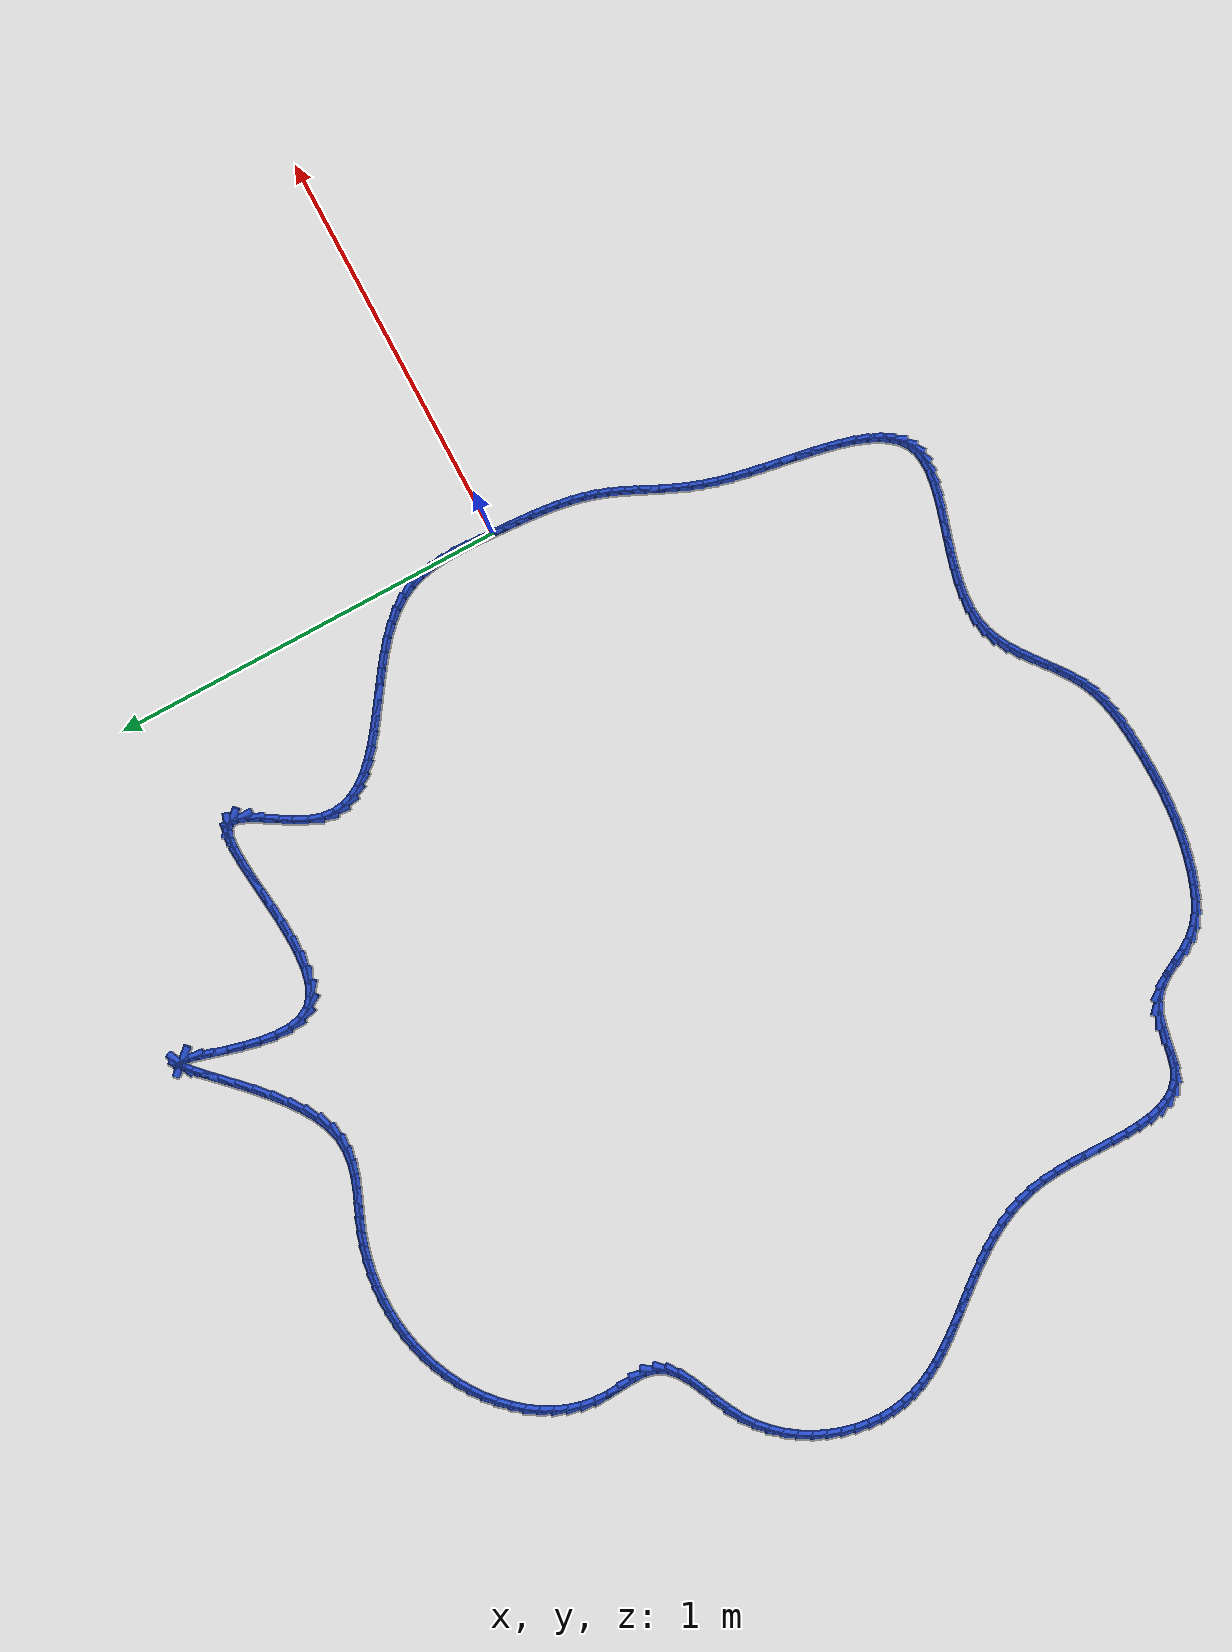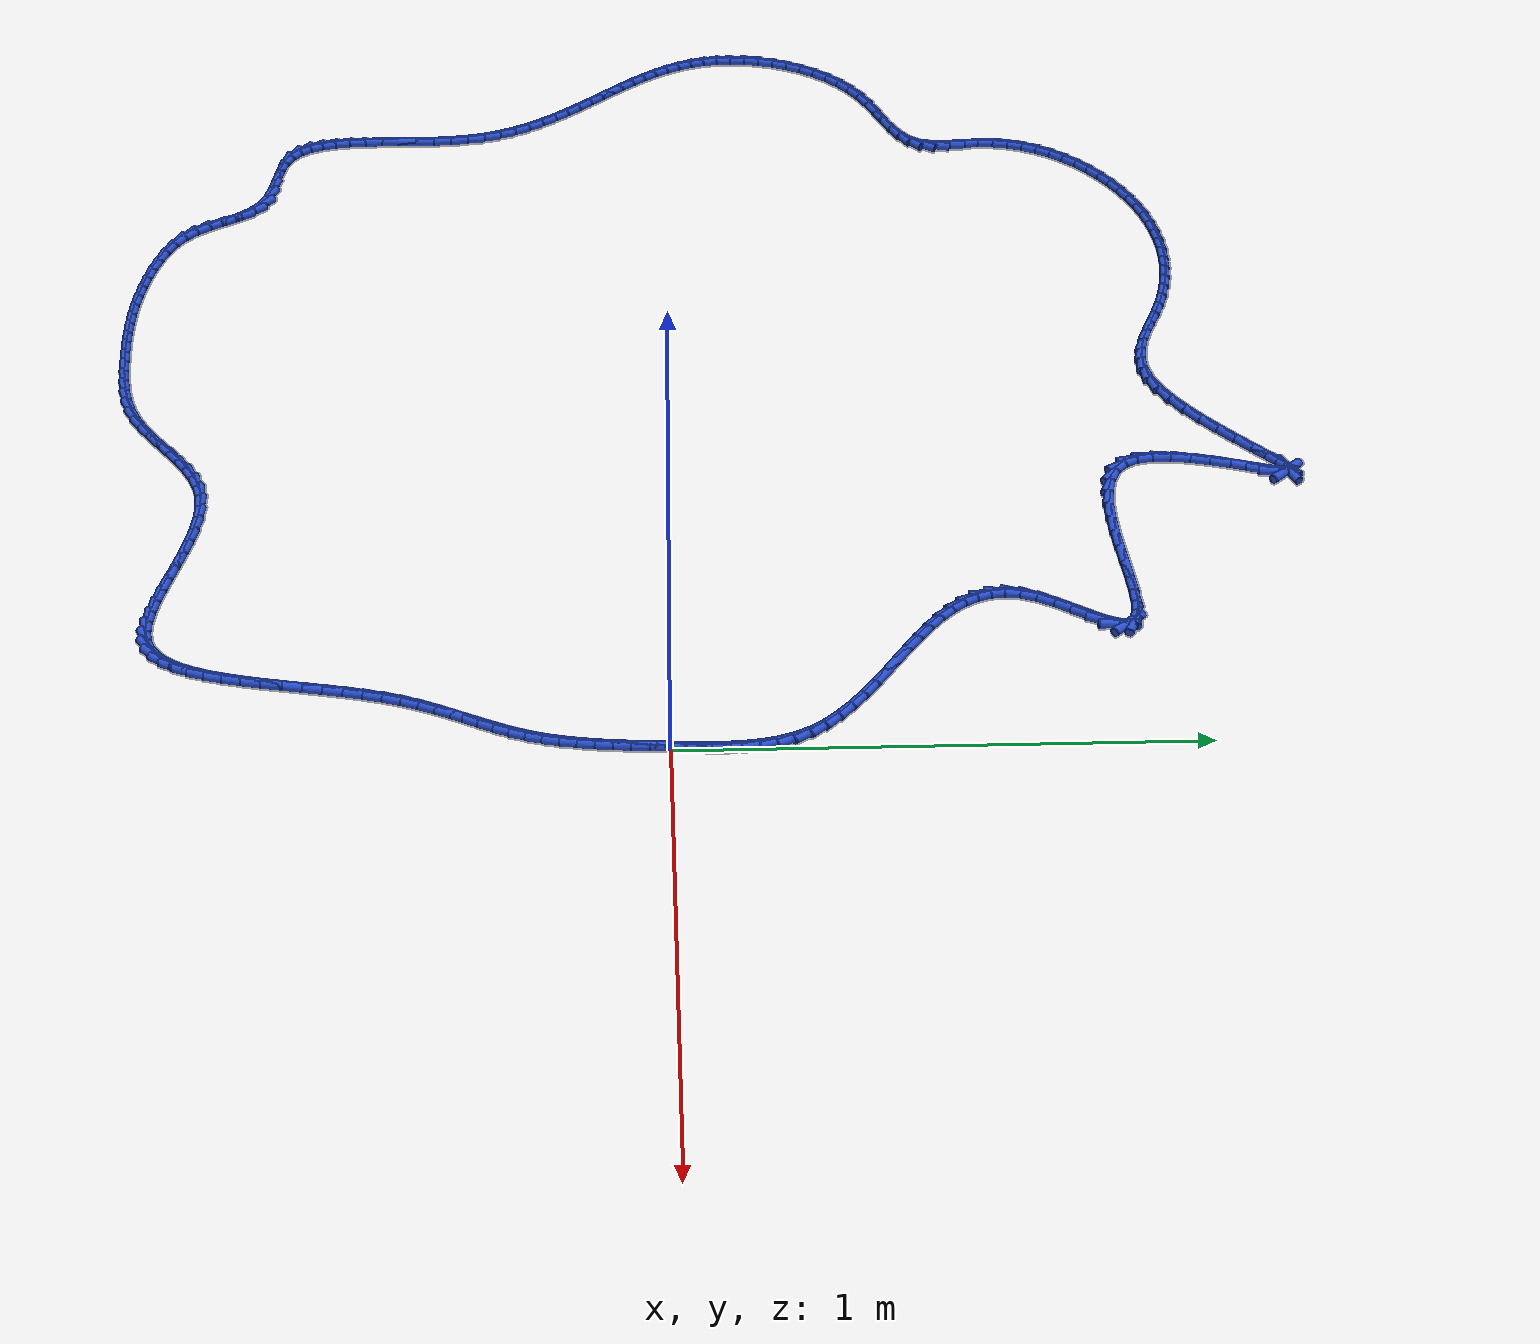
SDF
<sdf version="1.6">
 <world name="default">
  <light name="sun" type="directional">
   <pose>0 0 10 0 -0 0</pose>
   <diffuse>0.8 0.8 0.8 1</diffuse>
   <specular>0.2 0.2 0.2 1</specular>
   <attenuation>
    <range>1000</range>
    <constant>0.9</constant>
    <linear>0.01</linear>
    <quadratic>0.001</quadratic>
   </attenuation>
   <direction>-0.5 0.1 -0.9</direction>
  </light>
  <model name="ground_plane">
   <static>1</static>
   <link name="link">
    <collision name="collision">
     <geometry><plane><normal>0 0 1</normal><size>100 100</size></plane></geometry>
     <surface><friction><ode><mu>100</mu><mu2>50</mu2></ode></friction></surface>
    </collision>
    <visual name="visual">
     <cast_shadows>0</cast_shadows>
     <geometry><plane><normal>0 0 1</normal><size>100 100</size></plane></geometry>
     <material>
      <script><uri>file://media/materials/scripts/gazebo.material</uri><name>Gazebo/WhiteGlow</name></script>
     </material>
    </visual>
   </link>
  </model>
  <gravity>0 0 -9.8</gravity>
  <magnetic_field>6e-06 2.3e-05 -4.2e-05</magnetic_field>
  <atmosphere type="adiabatic"/>
  <physics name="default_physics" default="0" type="ode">
   <max_step_size>0.001</max_step_size>
   <real_time_factor>1</real_time_factor>
   <real_time_update_rate>1000</real_time_update_rate>
  </physics>
  <scene><ambient>0.4 0.4 0.4 1</ambient><background>0.7 0.7 0.7 1</background><shadows>1</shadows></scene>
  <spherical_coordinates>
   <surface_model>EARTH_WGS84</surface_model>
   <latitude_deg>0</latitude_deg>
   <longitude_deg>0</longitude_deg>
   <elevation>0</elevation>
   <heading_deg>0</heading_deg>
  </spherical_coordinates>
  <model name="line">
   <link name="link_0">
    <pose>-8.673617379884035e-19 -2.0816681711721685e-17 0.01 0 1.57 1.5201943071209887</pose>
    <collision name="collision">
     <geometry><cylinder><radius>0.01</radius><length>0.08</length></cylinder></geometry>
    </collision>
    <visual name="visual">
     <material>
      <script><name>Gazebo/Blue</name><uri>file://media/materials/scripts/gazebo.material</uri></script>
     </material>
     <geometry><cylinder><radius>0.01</radius><length>0.08</length></cylinder></geometry>
    </visual>
   </link>
   <link name="link_1">
    <pose>0.001718137990329249 0.033924955631097306 0.01 0 1.57 1.5356808636149406</pose>
    <collision name="collision">
     <geometry><cylinder><radius>0.01</radius><length>0.08</length></cylinder></geometry>
    </collision>
    <visual name="visual">
     <material>
      <script><name>Gazebo/Blue</name><uri>file://media/materials/scripts/gazebo.material</uri></script>
     </material>
     <geometry><cylinder><radius>0.01</radius><length>0.08</length></cylinder></geometry>
    </visual>
   </link>
   <link name="link_2">
    <pose>0.0029085599110991543 0.0678112402299358 0.01 0 1.57 1.5683742261349907</pose>
    <collision name="collision">
     <geometry><cylinder><radius>0.01</radius><length>0.08</length></cylinder></geometry>
    </collision>
    <visual name="visual">
     <material>
      <script><name>Gazebo/Blue</name><uri>file://media/materials/scripts/gazebo.material</uri></script>
     </material>
     <geometry><cylinder><radius>0.01</radius><length>0.08</length></cylinder></geometry>
    </visual>
   </link>
   <link name="link_3">
    <pose>0.002990008500110478 0.1014384263683361 0.01 0 1.57 -1.5223005778639336</pose>
    <collision name="collision">
     <geometry><cylinder><radius>0.01</radius><length>0.08</length></cylinder></geometry>
    </collision>
    <visual name="visual">
     <material>
      <script><name>Gazebo/Blue</name><uri>file://media/materials/scripts/gazebo.material</uri></script>
     </material>
     <geometry><cylinder><radius>0.01</radius><length>0.08</length></cylinder></geometry>
    </visual>
   </link>
   <link name="link_4">
    <pose>0.0013812264951639846 0.13458608661811874 0.01 0 1.57 -1.4517762006851882</pose>
    <collision name="collision">
     <geometry><cylinder><radius>0.01</radius><length>0.08</length></cylinder></geometry>
    </collision>
    <visual name="visual">
     <material>
      <script><name>Gazebo/Blue</name><uri>file://media/materials/scripts/gazebo.material</uri></script>
     </material>
     <geometry><cylinder><radius>0.01</radius><length>0.08</length></cylinder></geometry>
    </visual>
   </link>
   <link name="link_5">
    <pose>-0.0024990433659395593 0.16703379355110443 0.01 0 1.57 -1.3603957612050444</pose>
    <collision name="collision">
     <geometry><cylinder><radius>0.01</radius><length>0.08</length></cylinder></geometry>
    </collision>
    <visual name="visual">
     <material>
      <script><name>Gazebo/Blue</name><uri>file://media/materials/scripts/gazebo.material</uri></script>
     </material>
     <geometry><cylinder><radius>0.01</radius><length>0.08</length></cylinder></geometry>
    </visual>
   </link>
   <link name="link_6">
    <pose>-0.009232058345399396 0.19856111973911383 0.01 0 1.57 -1.247915427071994</pose>
    <collision name="collision">
     <geometry><cylinder><radius>0.01</radius><length>0.08</length></cylinder></geometry>
    </collision>
    <visual name="visual">
     <material>
      <script><name>Gazebo/Blue</name><uri>file://media/materials/scripts/gazebo.material</uri></script>
     </material>
     <geometry><cylinder><radius>0.01</radius><length>0.08</length></cylinder></geometry>
    </visual>
   </link>
   <link name="link_7">
    <pose>-0.01939907570541475 0.22894763775396743 0.01 0 1.57 -1.1162956648636326</pose>
    <collision name="collision">
     <geometry><cylinder><radius>0.01</radius><length>0.08</length></cylinder></geometry>
    </collision>
    <visual name="visual">
     <material>
      <script><name>Gazebo/Blue</name><uri>file://media/materials/scripts/gazebo.material</uri></script>
     </material>
     <geometry><cylinder><radius>0.01</radius><length>0.08</length></cylinder></geometry>
    </visual>
   </link>
   <link name="link_8">
    <pose>-0.033581352708184874 0.25797292016748574 0.01 0 1.57 -0.9766780912579256</pose>
    <collision name="collision">
     <geometry><cylinder><radius>0.01</radius><length>0.08</length></cylinder></geometry>
    </collision>
    <visual name="visual">
     <material>
      <script><name>Gazebo/Blue</name><uri>file://media/materials/scripts/gazebo.material</uri></script>
     </material>
     <geometry><cylinder><radius>0.01</radius><length>0.08</length></cylinder></geometry>
    </visual>
   </link>
   <link name="link_9">
    <pose>-0.0521642981769794 0.28548134029088046 0.01 0 1.57 -0.8594447137796409</pose>
    <collision name="collision">
     <geometry><cylinder><radius>0.01</radius><length>0.08</length></cylinder></geometry>
    </collision>
    <visual name="visual">
     <material>
      <script><name>Gazebo/Blue</name><uri>file://media/materials/scripts/gazebo.material</uri></script>
     </material>
     <geometry><cylinder><radius>0.01</radius><length>0.08</length></cylinder></geometry>
    </visual>
   </link>
   <link name="link_10">
    <pose>-0.07467622980034888 0.3116008587825914 0.01 0 1.57 -0.7696369081644873</pose>
    <collision name="collision">
     <geometry><cylinder><radius>0.01</radius><length>0.08</length></cylinder></geometry>
    </collision>
    <visual name="visual">
     <material>
      <script><name>Gazebo/Blue</name><uri>file://media/materials/scripts/gazebo.material</uri></script>
     </material>
     <geometry><cylinder><radius>0.01</radius><length>0.08</length></cylinder></geometry>
    </visual>
   </link>
   <link name="link_11">
    <pose>-0.10041106726462837 0.33653699200657455 0.01 0 1.57 -0.7033495402415681</pose>
    <collision name="collision">
     <geometry><cylinder><radius>0.01</radius><length>0.08</length></cylinder></geometry>
    </collision>
    <visual name="visual">
     <material>
      <script><name>Gazebo/Blue</name><uri>file://media/materials/scripts/gazebo.material</uri></script>
     </material>
     <geometry><cylinder><radius>0.01</radius><length>0.08</length></cylinder></geometry>
    </visual>
   </link>
   <link name="link_12">
    <pose>-0.128662724489709 0.3604952582347396 0.01 0 1.57 -0.6569692025207479</pose>
    <collision name="collision">
     <geometry><cylinder><radius>0.01</radius><length>0.08</length></cylinder></geometry>
    </collision>
    <visual name="visual">
     <material>
      <script><name>Gazebo/Blue</name><uri>file://media/materials/scripts/gazebo.material</uri></script>
     </material>
     <geometry><cylinder><radius>0.01</radius><length>0.08</length></cylinder></geometry>
    </visual>
   </link>
   <link name="link_13">
    <pose>-0.15872511539548156 0.3836811757389963 0.01 0 1.57 -0.627791398620207</pose>
    <collision name="collision">
     <geometry><cylinder><radius>0.01</radius><length>0.08</length></cylinder></geometry>
    </collision>
    <visual name="visual">
     <material>
      <script><name>Gazebo/Blue</name><uri>file://media/materials/scripts/gazebo.material</uri></script>
     </material>
     <geometry><cylinder><radius>0.01</radius><length>0.08</length></cylinder></geometry>
    </visual>
   </link>
   <link name="link_14">
    <pose>-0.18989215390183722 0.4063002627912545 0.01 0 1.57 -0.6141590037104268</pose>
    <collision name="collision">
     <geometry><cylinder><radius>0.01</radius><length>0.08</length></cylinder></geometry>
    </collision>
    <visual name="visual">
     <material>
      <script><name>Gazebo/Blue</name><uri>file://media/materials/scripts/gazebo.material</uri></script>
     </material>
     <geometry><cylinder><radius>0.01</radius><length>0.08</length></cylinder></geometry>
    </visual>
   </link>
   <link name="link_15">
    <pose>-0.22145775392866693 0.42855803766342376 0.01 0 1.57 -0.6154623014193488</pose>
    <collision name="collision">
     <geometry><cylinder><radius>0.01</radius><length>0.08</length></cylinder></geometry>
    </collision>
    <visual name="visual">
     <material>
      <script><name>Gazebo/Blue</name><uri>file://media/materials/scripts/gazebo.material</uri></script>
     </material>
     <geometry><cylinder><radius>0.01</radius><length>0.08</length></cylinder></geometry>
    </visual>
   </link>
   <link name="link_16">
    <pose>-0.25271582939586185 0.4506600186274141 0.01 0 1.57 -0.6321558162892793</pose>
    <collision name="collision">
     <geometry><cylinder><radius>0.01</radius><length>0.08</length></cylinder></geometry>
    </collision>
    <visual name="visual">
     <material>
      <script><name>Gazebo/Blue</name><uri>file://media/materials/scripts/gazebo.material</uri></script>
     </material>
     <geometry><cylinder><radius>0.01</radius><length>0.08</length></cylinder></geometry>
    </visual>
   </link>
   <link name="link_17">
    <pose>-0.28296029422331276 0.4728117239551351 0.01 0 1.57 -0.665852831374529</pose>
    <collision name="collision">
     <geometry><cylinder><radius>0.01</radius><length>0.08</length></cylinder></geometry>
    </collision>
    <visual name="visual">
     <material>
      <script><name>Gazebo/Blue</name><uri>file://media/materials/scripts/gazebo.material</uri></script>
     </material>
     <geometry><cylinder><radius>0.01</radius><length>0.08</length></cylinder></geometry>
    </visual>
   </link>
   <link name="link_18">
    <pose>-0.3114850623309109 0.49521867191849667 0.01 0 1.57 -0.7195044284954116</pose>
    <collision name="collision">
     <geometry><cylinder><radius>0.01</radius><length>0.08</length></cylinder></geometry>
    </collision>
    <visual name="visual">
     <material>
      <script><name>Gazebo/Blue</name><uri>file://media/materials/scripts/gazebo.material</uri></script>
     </material>
     <geometry><cylinder><radius>0.01</radius><length>0.08</length></cylinder></geometry>
    </visual>
   </link>
   <link name="link_19">
    <pose>-0.3375840476385471 0.5180863807894086 0.01 0 1.57 -0.7975880576177107</pose>
    <collision name="collision">
     <geometry><cylinder><radius>0.01</radius><length>0.08</length></cylinder></geometry>
    </collision>
    <visual name="visual">
     <material>
      <script><name>Gazebo/Blue</name><uri>file://media/materials/scripts/gazebo.material</uri></script>
     </material>
     <geometry><cylinder><radius>0.01</radius><length>0.08</length></cylinder></geometry>
    </visual>
   </link>
   <link name="link_20">
    <pose>-0.3605511640661126 0.5416203688397805 0.01 0 1.57 -0.9060141525620757</pose>
    <collision name="collision">
     <geometry><cylinder><radius>0.01</radius><length>0.08</length></cylinder></geometry>
    </collision>
    <visual name="visual">
     <material>
      <script><name>Gazebo/Blue</name><uri>file://media/materials/scripts/gazebo.material</uri></script>
     </material>
     <geometry><cylinder><radius>0.01</radius><length>0.08</length></cylinder></geometry>
    </visual>
   </link>
   <link name="link_21">
    <pose>-0.37968032553349823 0.5660261543415224 0.01 0 1.57 -1.0509597911585271</pose>
    <collision name="collision">
     <geometry><cylinder><radius>0.01</radius><length>0.08</length></cylinder></geometry>
    </collision>
    <visual name="visual">
     <material>
      <script><name>Gazebo/Blue</name><uri>file://media/materials/scripts/gazebo.material</uri></script>
     </material>
     <geometry><cylinder><radius>0.01</radius><length>0.08</length></cylinder></geometry>
    </visual>
   </link>
   <link name="link_22">
    <pose>-0.39426544596059515 0.5915092555665439 0.01 0 1.57 -1.2352230891861422</pose>
    <collision name="collision">
     <geometry><cylinder><radius>0.01</radius><length>0.08</length></cylinder></geometry>
    </collision>
    <visual name="visual">
     <material>
      <script><name>Gazebo/Blue</name><uri>file://media/materials/scripts/gazebo.material</uri></script>
     </material>
     <geometry><cylinder><radius>0.01</radius><length>0.08</length></cylinder></geometry>
    </visual>
   </link>
   <link name="link_23">
    <pose>-0.4036004392672942 0.6182751907867547 0.01 0 1.57 -1.451776838935405</pose>
    <collision name="collision">
     <geometry><cylinder><radius>0.01</radius><length>0.08</length></cylinder></geometry>
    </collision>
    <visual name="visual">
     <material>
      <script><name>Gazebo/Blue</name><uri>file://media/materials/scripts/gazebo.material</uri></script>
     </material>
     <geometry><cylinder><radius>0.01</radius><length>0.08</length></cylinder></geometry>
    </visual>
   </link>
   <link name="link_24">
    <pose>-0.4069792193734867 0.6465294782740649 0.01 0 1.57 1.461592406780815</pose>
    <collision name="collision">
     <geometry><cylinder><radius>0.01</radius><length>0.08</length></cylinder></geometry>
    </collision>
    <visual name="visual">
     <material>
      <script><name>Gazebo/Blue</name><uri>file://media/materials/scripts/gazebo.material</uri></script>
     </material>
     <geometry><cylinder><radius>0.01</radius><length>0.08</length></cylinder></geometry>
    </visual>
   </link>
   <link name="link_25">
    <pose>-0.40369570019906315 0.6764776363003837 0.01 0 1.57 1.2510227166018464</pose>
    <collision name="collision">
     <geometry><cylinder><radius>0.01</radius><length>0.08</length></cylinder></geometry>
    </collision>
    <visual name="visual">
     <material>
      <script><name>Gazebo/Blue</name><uri>file://media/materials/scripts/gazebo.material</uri></script>
     </material>
     <geometry><cylinder><radius>0.01</radius><length>0.08</length></cylinder></geometry>
    </visual>
   </link>
   <link name="link_26">
    <pose>-0.3931671148218804 0.70827277879854 0.01 0 1.57 1.1098068839510666</pose>
    <collision name="collision">
     <geometry><cylinder><radius>0.01</radius><length>0.08</length></cylinder></geometry>
    </collision>
    <visual name="visual">
     <material>
      <script><name>Gazebo/Blue</name><uri>file://media/materials/scripts/gazebo.material</uri></script>
     </material>
     <geometry><cylinder><radius>0.01</radius><length>0.08</length></cylinder></geometry>
    </visual>
   </link>
   <link name="link_27">
    <pose>-0.37680191188064943 0.741221854862436 0.01 0 1.57 1.0406158870156996</pose>
    <collision name="collision">
     <geometry><cylinder><radius>0.01</radius><length>0.08</length></cylinder></geometry>
    </collision>
    <visual name="visual">
     <material>
      <script><name>Gazebo/Blue</name><uri>file://media/materials/scripts/gazebo.material</uri></script>
     </material>
     <geometry><cylinder><radius>0.01</radius><length>0.08</length></cylinder></geometry>
    </visual>
   </link>
   <link name="link_28">
    <pose>-0.3576196601141881 0.7739471698905402 0.01 0 1.57 1.0239956971512725</pose>
    <collision name="collision">
     <geometry><cylinder><radius>0.01</radius><length>0.08</length></cylinder></geometry>
    </collision>
    <visual name="visual">
     <material>
      <script><name>Gazebo/Blue</name><uri>file://media/materials/scripts/gazebo.material</uri></script>
     </material>
     <geometry><cylinder><radius>0.01</radius><length>0.08</length></cylinder></geometry>
    </visual>
   </link>
   <link name="link_29">
    <pose>-0.33868615756294174 0.8050513841909855 0.01 0 1.57 1.063269467934556</pose>
    <collision name="collision">
     <geometry><cylinder><radius>0.01</radius><length>0.08</length></cylinder></geometry>
    </collision>
    <visual name="visual">
     <material>
      <script><name>Gazebo/Blue</name><uri>file://media/materials/scripts/gazebo.material</uri></script>
     </material>
     <geometry><cylinder><radius>0.01</radius><length>0.08</length></cylinder></geometry>
    </visual>
   </link>
   <link name="link_30">
    <pose>-0.3230672022673562 0.8331371580719068 0.01 0 1.57 1.1986721337319537</pose>
    <collision name="collision">
     <geometry><cylinder><radius>0.01</radius><length>0.08</length></cylinder></geometry>
    </collision>
    <visual name="visual">
     <material>
      <script><name>Gazebo/Blue</name><uri>file://media/materials/scripts/gazebo.material</uri></script>
     </material>
     <geometry><cylinder><radius>0.01</radius><length>0.08</length></cylinder></geometry>
    </visual>
   </link>
   <link name="link_31">
    <pose>-0.31382859226787707 0.8568071518414377 0.01 0 1.57 -1.564745702820627</pose>
    <collision name="collision">
     <geometry><cylinder><radius>0.01</radius><length>0.08</length></cylinder></geometry>
    </collision>
    <visual name="visual">
     <material>
      <script><name>Gazebo/Blue</name><uri>file://media/materials/scripts/gazebo.material</uri></script>
     </material>
     <geometry><cylinder><radius>0.01</radius><length>0.08</length></cylinder></geometry>
    </visual>
   </link>
   <link name="link_32">
    <pose>-0.31393695750646217 0.8747166958196684 0.01 0 1.57 -0.8600478975879854</pose>
    <collision name="collision">
     <geometry><cylinder><radius>0.01</radius><length>0.08</length></cylinder></geometry>
    </collision>
    <visual name="visual">
     <material>
      <script><name>Gazebo/Blue</name><uri>file://media/materials/scripts/gazebo.material</uri></script>
     </material>
     <geometry><cylinder><radius>0.01</radius><length>0.08</length></cylinder></geometry>
    </visual>
   </link>
   <link name="link_33">
    <pose>-0.32421702462953694 0.8866587247973424 0.01 0 1.57 -0.3432603674694427</pose>
    <collision name="collision">
     <geometry><cylinder><radius>0.01</radius><length>0.08</length></cylinder></geometry>
    </collision>
    <visual name="visual">
     <material>
      <script><name>Gazebo/Blue</name><uri>file://media/materials/scripts/gazebo.material</uri></script>
     </material>
     <geometry><cylinder><radius>0.01</radius><length>0.08</length></cylinder></geometry>
    </visual>
   </link>
   <link name="link_34">
    <pose>-0.34342608718736506 0.893524225535088 0.01 0 1.57 -0.10127875479051505</pose>
    <collision name="collision">
     <geometry><cylinder><radius>0.01</radius><length>0.08</length></cylinder></geometry>
    </collision>
    <visual name="visual">
     <material>
      <script><name>Gazebo/Blue</name><uri>file://media/materials/scripts/gazebo.material</uri></script>
     </material>
     <geometry><cylinder><radius>0.01</radius><length>0.08</length></cylinder></geometry>
    </visual>
   </link>
   <link name="link_35">
    <pose>-0.3702371705185636 0.8962489411999063 0.01 0 1.57 0.014516430586478975</pose>
    <collision name="collision">
     <geometry><cylinder><radius>0.01</radius><length>0.08</length></cylinder></geometry>
    </collision>
    <visual name="visual">
     <material>
      <script><name>Gazebo/Blue</name><uri>file://media/materials/scripts/gazebo.material</uri></script>
     </material>
     <geometry><cylinder><radius>0.01</radius><length>0.08</length></cylinder></geometry>
    </visual>
   </link>
   <link name="link_36">
    <pose>-0.4033232999617488 0.895768614958798 0.01 0 1.57 0.07216793609204356</pose>
    <collision name="collision">
     <geometry><cylinder><radius>0.01</radius><length>0.08</length></cylinder></geometry>
    </collision>
    <visual name="visual">
     <material>
      <script><name>Gazebo/Blue</name><uri>file://media/materials/scripts/gazebo.material</uri></script>
     </material>
     <geometry><cylinder><radius>0.01</radius><length>0.08</length></cylinder></geometry>
    </visual>
   </link>
   <link name="link_37">
    <pose>-0.4413575008555378 0.893018989978764 0.01 0 1.57 0.09771092466176137</pose>
    <collision name="collision">
     <geometry><cylinder><radius>0.01</radius><length>0.08</length></cylinder></geometry>
    </collision>
    <visual name="visual">
     <material>
      <script><name>Gazebo/Blue</name><uri>file://media/materials/scripts/gazebo.material</uri></script>
     </material>
     <geometry><cylinder><radius>0.01</radius><length>0.08</length></cylinder></geometry>
    </visual>
   </link>
   <link name="link_38">
    <pose>-0.4830127985385472 0.8889358094268056 0.01 0 1.57 0.10160684340311654</pose>
    <collision name="collision">
     <geometry><cylinder><radius>0.01</radius><length>0.08</length></cylinder></geometry>
    </collision>
    <visual name="visual">
     <material>
      <script><name>Gazebo/Blue</name><uri>file://media/materials/scripts/gazebo.material</uri></script>
     </material>
     <geometry><cylinder><radius>0.01</radius><length>0.08</length></cylinder></geometry>
    </visual>
   </link>
   <link name="link_39">
    <pose>-0.5269622183493937 0.8844548164699227 0.01 0 1.57 0.08756189560972612</pose>
    <collision name="collision">
     <geometry><cylinder><radius>0.01</radius><length>0.08</length></cylinder></geometry>
    </collision>
    <visual name="visual">
     <material>
      <script><name>Gazebo/Blue</name><uri>file://media/materials/scripts/gazebo.material</uri></script>
     </material>
     <geometry><cylinder><radius>0.01</radius><length>0.08</length></cylinder></geometry>
    </visual>
   </link>
   <link name="link_40">
    <pose>-0.5718787856266938 0.8805117542751173 0.01 0 1.57 0.055364567964254596</pose>
    <collision name="collision">
     <geometry><cylinder><radius>0.01</radius><length>0.08</length></cylinder></geometry>
    </collision>
    <visual name="visual">
     <material>
      <script><name>Gazebo/Blue</name><uri>file://media/materials/scripts/gazebo.material</uri></script>
     </material>
     <geometry><cylinder><radius>0.01</radius><length>0.08</length></cylinder></geometry>
    </visual>
   </link>
   <link name="link_41">
    <pose>-0.6164355257090647 0.8780423660093895 0.01 0 1.57 0.001398908722775671</pose>
    <collision name="collision">
     <geometry><cylinder><radius>0.01</radius><length>0.08</length></cylinder></geometry>
    </collision>
    <visual name="visual">
     <material>
      <script><name>Gazebo/Blue</name><uri>file://media/materials/scripts/gazebo.material</uri></script>
     </material>
     <geometry><cylinder><radius>0.01</radius><length>0.08</length></cylinder></geometry>
    </visual>
   </link>
   <link name="link_42">
    <pose>-0.6593054639351227 0.87798239483974 0.01 0 1.57 -0.08224021591113025</pose>
    <collision name="collision">
     <geometry><cylinder><radius>0.01</radius><length>0.08</length></cylinder></geometry>
    </collision>
    <visual name="visual">
     <material>
      <script><name>Gazebo/Blue</name><uri>file://media/materials/scripts/gazebo.material</uri></script>
     </material>
     <geometry><cylinder><radius>0.01</radius><length>0.08</length></cylinder></geometry>
    </visual>
   </link>
   <link name="link_43">
    <pose>-0.699161625643485 0.8812675839331703 0.01 0 1.57 -0.20989902813836786</pose>
    <collision name="collision">
     <geometry><cylinder><radius>0.01</radius><length>0.08</length></cylinder></geometry>
    </collision>
    <visual name="visual">
     <material>
      <script><name>Gazebo/Blue</name><uri>file://media/materials/scripts/gazebo.material</uri></script>
     </material>
     <geometry><cylinder><radius>0.01</radius><length>0.08</length></cylinder></geometry>
    </visual>
   </link>
   <link name="link_44">
    <pose>-0.7346770361727677 0.8888336764566808 0.01 0 1.57 -0.4046334568544427</pose>
    <collision name="collision">
     <geometry><cylinder><radius>0.01</radius><length>0.08</length></cylinder></geometry>
    </collision>
    <visual name="visual">
     <material>
      <script><name>Gazebo/Blue</name><uri>file://media/materials/scripts/gazebo.material</uri></script>
     </material>
     <geometry><cylinder><radius>0.01</radius><length>0.08</length></cylinder></geometry>
    </visual>
   </link>
   <link name="link_45">
    <pose>-0.7645247208615878 0.9016164155772723 0.01 0 1.57 -0.691916170527639</pose>
    <collision name="collision">
     <geometry><cylinder><radius>0.01</radius><length>0.08</length></cylinder></geometry>
    </collision>
    <visual name="visual">
     <material>
      <script><name>Gazebo/Blue</name><uri>file://media/materials/scripts/gazebo.material</uri></script>
     </material>
     <geometry><cylinder><radius>0.01</radius><length>0.08</length></cylinder></geometry>
    </visual>
   </link>
   <link name="link_46">
    <pose>-0.7873777050485621 0.9205515444619459 0.01 0 1.57 -1.0583537056594072</pose>
    <collision name="collision">
     <geometry><cylinder><radius>0.01</radius><length>0.08</length></cylinder></geometry>
    </collision>
    <visual name="visual">
     <material>
      <script><name>Gazebo/Blue</name><uri>file://media/materials/scripts/gazebo.material</uri></script>
     </material>
     <geometry><cylinder><radius>0.01</radius><length>0.08</length></cylinder></geometry>
    </visual>
   </link>
   <link name="link_47">
    <pose>-0.8019790105620597 0.9465061917876808 0.01 0 1.57 -1.3720409962248215</pose>
    <collision name="collision">
     <geometry><cylinder><radius>0.01</radius><length>0.08</length></cylinder></geometry>
    </collision>
    <visual name="visual">
     <material>
      <script><name>Gazebo/Blue</name><uri>file://media/materials/scripts/gazebo.material</uri></script>
     </material>
     <geometry><cylinder><radius>0.01</radius><length>0.08</length></cylinder></geometry>
    </visual>
   </link>
   <link name="link_48">
    <pose>-0.8085109659351283 0.9789365969729197 0.01 0 1.57 1.570671844928276</pose>
    <collision name="collision">
     <geometry><cylinder><radius>0.01</radius><length>0.08</length></cylinder></geometry>
    </collision>
    <visual name="visual">
     <material>
      <script><name>Gazebo/Blue</name><uri>file://media/materials/scripts/gazebo.material</uri></script>
     </material>
     <geometry><cylinder><radius>0.01</radius><length>0.08</length></cylinder></geometry>
    </visual>
   </link>
   <link name="link_49">
    <pose>-0.8085063552997886 1.0159752070209616 0.01 0 1.57 1.4466847730902823</pose>
    <collision name="collision">
     <geometry><cylinder><radius>0.01</radius><length>0.08</length></cylinder></geometry>
    </collision>
    <visual name="visual">
     <material>
      <script><name>Gazebo/Blue</name><uri>file://media/materials/scripts/gazebo.material</uri></script>
     </material>
     <geometry><cylinder><radius>0.01</radius><length>0.08</length></cylinder></geometry>
    </visual>
   </link>
   <link name="link_50">
    <pose>-0.8035501664358974 1.055703295987915 0.01 0 1.57 1.3681116096140662</pose>
    <collision name="collision">
     <geometry><cylinder><radius>0.01</radius><length>0.08</length></cylinder></geometry>
    </collision>
    <visual name="visual">
     <material>
      <script><name>Gazebo/Blue</name><uri>file://media/materials/scripts/gazebo.material</uri></script>
     </material>
     <geometry><cylinder><radius>0.01</radius><length>0.08</length></cylinder></geometry>
    </visual>
   </link>
   <link name="link_51">
    <pose>-0.7952273871233129 1.096202137929888 0.01 0 1.57 1.3194499353170774</pose>
    <collision name="collision">
     <geometry><cylinder><radius>0.01</radius><length>0.08</length></cylinder></geometry>
    </collision>
    <visual name="visual">
     <material>
      <script><name>Gazebo/Blue</name><uri>file://media/materials/scripts/gazebo.material</uri></script>
     </material>
     <geometry><cylinder><radius>0.01</radius><length>0.08</length></cylinder></geometry>
    </visual>
   </link>
   <link name="link_52">
    <pose>-0.7851230051418924 1.1355530069029904 0.01 0 1.57 1.2941768440676495</pose>
    <collision name="collision">
     <geometry><cylinder><radius>0.01</radius><length>0.08</length></cylinder></geometry>
    </collision>
    <visual name="visual">
     <material>
      <script><name>Gazebo/Blue</name><uri>file://media/materials/scripts/gazebo.material</uri></script>
     </material>
     <geometry><cylinder><radius>0.01</radius><length>0.08</length></cylinder></geometry>
    </visual>
   </link>
   <link name="link_53">
    <pose>-0.7748220082714931 1.1718371769633291 0.01 0 1.57 1.2933793523130341</pose>
    <collision name="collision">
     <geometry><cylinder><radius>0.01</radius><length>0.08</length></cylinder></geometry>
    </collision>
    <visual name="visual">
     <material>
      <script><name>Gazebo/Blue</name><uri>file://media/materials/scripts/gazebo.material</uri></script>
     </material>
     <geometry><cylinder><radius>0.01</radius><length>0.08</length></cylinder></geometry>
    </visual>
   </link>
   <link name="link_54">
    <pose>-0.7659093842919726 1.203135922167014 0.01 0 1.57 1.3319763541267404</pose>
    <collision name="collision">
     <geometry><cylinder><radius>0.01</radius><length>0.08</length></cylinder></geometry>
    </collision>
    <visual name="visual">
     <material>
      <script><name>Gazebo/Blue</name><uri>file://media/materials/scripts/gazebo.material</uri></script>
     </material>
     <geometry><cylinder><radius>0.01</radius><length>0.08</length></cylinder></geometry>
    </visual>
   </link>
   <link name="link_55">
    <pose>-0.7599701209831887 1.2275305165701527 0.01 0 1.57 1.4823467483856345</pose>
    <collision name="collision">
     <geometry><cylinder><radius>0.01</radius><length>0.08</length></cylinder></geometry>
    </collision>
    <visual name="visual">
     <material>
      <script><name>Gazebo/Blue</name><uri>file://media/materials/scripts/gazebo.material</uri></script>
     </material>
     <geometry><cylinder><radius>0.01</radius><length>0.08</length></cylinder></geometry>
    </visual>
   </link>
   <link name="link_56">
    <pose>-0.7585892061249982 1.2431022342288536 0.01 0 1.57 -0.8506377276693793</pose>
    <collision name="collision">
     <geometry><cylinder><radius>0.01</radius><length>0.08</length></cylinder></geometry>
    </collision>
    <visual name="visual">
     <material>
      <script><name>Gazebo/Blue</name><uri>file://media/materials/scripts/gazebo.material</uri></script>
     </material>
     <geometry><cylinder><radius>0.01</radius><length>0.08</length></cylinder></geometry>
    </visual>
   </link>
   <link name="link_57">
    <pose>-0.763131385225953 1.2482794003074016 0.01 0 1.57 0.41182475326074186</pose>
    <collision name="collision">
     <geometry><cylinder><radius>0.01</radius><length>0.08</length></cylinder></geometry>
    </collision>
    <visual name="visual">
     <material>
      <script><name>Gazebo/Blue</name><uri>file://media/materials/scripts/gazebo.material</uri></script>
     </material>
     <geometry><cylinder><radius>0.01</radius><length>0.08</length></cylinder></geometry>
    </visual>
   </link>
   <link name="link_58">
    <pose>-0.7735375877520306 1.2437339462155288 0.01 0 1.57 0.6820222823260549</pose>
    <collision name="collision">
     <geometry><cylinder><radius>0.01</radius><length>0.08</length></cylinder></geometry>
    </collision>
    <visual name="visual">
     <material>
      <script><name>Gazebo/Blue</name><uri>file://media/materials/scripts/gazebo.material</uri></script>
     </material>
     <geometry><cylinder><radius>0.01</radius><length>0.08</length></cylinder></geometry>
    </visual>
   </link>
   <link name="link_59">
    <pose>-0.7891824684333627 1.2310301219603068 0.01 0 1.57 0.7611034894928629</pose>
    <collision name="collision">
     <geometry><cylinder><radius>0.01</radius><length>0.08</length></cylinder></geometry>
    </collision>
    <visual name="visual">
     <material>
      <script><name>Gazebo/Blue</name><uri>file://media/materials/scripts/gazebo.material</uri></script>
     </material>
     <geometry><cylinder><radius>0.01</radius><length>0.08</length></cylinder></geometry>
    </visual>
   </link>
   <link name="link_60">
    <pose>-0.8094392346653811 1.2117344582150462 0.01 0 1.57 0.7870272552570731</pose>
    <collision name="collision">
     <geometry><cylinder><radius>0.01</radius><length>0.08</length></cylinder></geometry>
    </collision>
    <visual name="visual">
     <material>
      <script><name>Gazebo/Blue</name><uri>file://media/materials/scripts/gazebo.material</uri></script>
     </material>
     <geometry><cylinder><radius>0.01</radius><length>0.08</length></cylinder></geometry>
    </visual>
   </link>
   <link name="link_61">
    <pose>-0.833681093843516 1.1874134856530558 0.01 0 1.57 0.7886410461585955</pose>
    <collision name="collision">
     <geometry><cylinder><radius>0.01</radius><length>0.08</length></cylinder></geometry>
    </collision>
    <visual name="visual">
     <material>
      <script><name>Gazebo/Blue</name><uri>file://media/materials/scripts/gazebo.material</uri></script>
     </material>
     <geometry><cylinder><radius>0.01</radius><length>0.08</length></cylinder></geometry>
    </visual>
   </link>
   <link name="link_62">
    <pose>-0.8612812533631987 1.1596337349476455 0.01 0 1.57 0.7744047932160668</pose>
    <collision name="collision">
     <geometry><cylinder><radius>0.01</radius><length>0.08</length></cylinder></geometry>
    </collision>
    <visual name="visual">
     <material>
      <script><name>Gazebo/Blue</name><uri>file://media/materials/scripts/gazebo.material</uri></script>
     </material>
     <geometry><cylinder><radius>0.01</radius><length>0.08</length></cylinder></geometry>
    </visual>
   </link>
   <link name="link_63">
    <pose>-0.8916129206198601 1.1299617367721244 0.01 0 1.57 0.7463581443893547</pose>
    <collision name="collision">
     <geometry><cylinder><radius>0.01</radius><length>0.08</length></cylinder></geometry>
    </collision>
    <visual name="visual">
     <material>
      <script><name>Gazebo/Blue</name><uri>file://media/materials/scripts/gazebo.material</uri></script>
     </material>
     <geometry><cylinder><radius>0.01</radius><length>0.08</length></cylinder></geometry>
    </visual>
   </link>
   <link name="link_64">
    <pose>-0.9240493030089306 1.0999640217998023 0.01 0 1.57 0.7032901428280318</pose>
    <collision name="collision">
     <geometry><cylinder><radius>0.01</radius><length>0.08</length></cylinder></geometry>
    </collision>
    <visual name="visual">
     <material>
      <script><name>Gazebo/Blue</name><uri>file://media/materials/scripts/gazebo.material</uri></script>
     </material>
     <geometry><cylinder><radius>0.01</radius><length>0.08</length></cylinder></geometry>
    </visual>
   </link>
   <link name="link_65">
    <pose>-0.9579636079258416 1.071207120703989 0.01 0 1.57 0.6412048729258841</pose>
    <collision name="collision">
     <geometry><cylinder><radius>0.01</radius><length>0.08</length></cylinder></geometry>
    </collision>
    <visual name="visual">
     <material>
      <script><name>Gazebo/Blue</name><uri>file://media/materials/scripts/gazebo.material</uri></script>
     </material>
     <geometry><cylinder><radius>0.01</radius><length>0.08</length></cylinder></geometry>
    </visual>
   </link>
   <link name="link_66">
    <pose>-0.9927290427660236 1.0452575641579929 0.01 0 1.57 0.55255650376366</pose>
    <collision name="collision">
     <geometry><cylinder><radius>0.01</radius><length>0.08</length></cylinder></geometry>
    </collision>
    <visual name="visual">
     <material>
      <script><name>Gazebo/Blue</name><uri>file://media/materials/scripts/gazebo.material</uri></script>
     </material>
     <geometry><cylinder><radius>0.01</radius><length>0.08</length></cylinder></geometry>
    </visual>
   </link>
   <link name="link_67">
    <pose>-1.0277188149249075 1.0236818828351246 0.01 0 1.57 0.4245592919007156</pose>
    <collision name="collision">
     <geometry><cylinder><radius>0.01</radius><length>0.08</length></cylinder></geometry>
    </collision>
    <visual name="visual">
     <material>
      <script><name>Gazebo/Blue</name><uri>file://media/materials/scripts/gazebo.material</uri></script>
     </material>
     <geometry><cylinder><radius>0.01</radius><length>0.08</length></cylinder></geometry>
    </visual>
   </link>
   <link name="link_68">
    <pose>-1.062306131797924 1.0080466074086933 0.01 0 1.57 0.24484322621479393</pose>
    <collision name="collision">
     <geometry><cylinder><radius>0.01</radius><length>0.08</length></cylinder></geometry>
    </collision>
    <visual name="visual">
     <material>
      <script><name>Gazebo/Blue</name><uri>file://media/materials/scripts/gazebo.material</uri></script>
     </material>
     <geometry><cylinder><radius>0.01</radius><length>0.08</length></cylinder></geometry>
    </visual>
   </link>
   <link name="link_69">
    <pose>-1.0959473746806214 0.9996411375568232 0.01 0 1.57 0.0519977294275255</pose>
    <collision name="collision">
     <geometry><cylinder><radius>0.01</radius><length>0.08</length></cylinder></geometry>
    </collision>
    <visual name="visual">
     <material>
      <script><name>Gazebo/Blue</name><uri>file://media/materials/scripts/gazebo.material</uri></script>
     </material>
     <geometry><cylinder><radius>0.01</radius><length>0.08</length></cylinder></geometry>
    </visual>
   </link>
   <link name="link_70">
    <pose>-1.1286437738846857 0.997939465121097 0.01 0 1.57 -0.11661330106158022</pose>
    <collision name="collision">
     <geometry><cylinder><radius>0.01</radius><length>0.08</length></cylinder></geometry>
    </collision>
    <visual name="visual">
     <material>
      <script><name>Gazebo/Blue</name><uri>file://media/materials/scripts/gazebo.material</uri></script>
     </material>
     <geometry><cylinder><radius>0.01</radius><length>0.08</length></cylinder></geometry>
    </visual>
   </link>
   <link name="link_71">
    <pose>-1.1606158764615333 1.0016848302739179 0.01 0 1.57 -0.24696367830435928</pose>
    <collision name="collision">
     <geometry><cylinder><radius>0.01</radius><length>0.08</length></cylinder></geometry>
    </collision>
    <visual name="visual">
     <material>
      <script><name>Gazebo/Blue</name><uri>file://media/materials/scripts/gazebo.material</uri></script>
     </material>
     <geometry><cylinder><radius>0.01</radius><length>0.08</length></cylinder></geometry>
    </visual>
   </link>
   <link name="link_72">
    <pose>-1.1920848300092128 1.0096184721983743 0.01 0 1.57 -0.33518077162889653</pose>
    <collision name="collision">
     <geometry><cylinder><radius>0.01</radius><length>0.08</length></cylinder></geometry>
    </collision>
    <visual name="visual">
     <material>
      <script><name>Gazebo/Blue</name><uri>file://media/materials/scripts/gazebo.material</uri></script>
     </material>
     <geometry><cylinder><radius>0.01</radius><length>0.08</length></cylinder></geometry>
    </visual>
   </link>
   <link name="link_73">
    <pose>-1.2232717821257721 1.0204816300775554 0.01 0 1.57 -0.38281612621059274</pose>
    <collision name="collision">
     <geometry><cylinder><radius>0.01</radius><length>0.08</length></cylinder></geometry>
    </collision>
    <visual name="visual">
     <material>
      <script><name>Gazebo/Blue</name><uri>file://media/materials/scripts/gazebo.material</uri></script>
     </material>
     <geometry><cylinder><radius>0.01</radius><length>0.08</length></cylinder></geometry>
    </visual>
   </link>
   <link name="link_74">
    <pose>-1.2543978804092595 1.0330155430945498 0.01 0 1.57 -0.39233507034282566</pose>
    <collision name="collision">
     <geometry><cylinder><radius>0.01</radius><length>0.08</length></cylinder></geometry>
    </collision>
    <visual name="visual">
     <material>
      <script><name>Gazebo/Blue</name><uri>file://media/materials/scripts/gazebo.material</uri></script>
     </material>
     <geometry><cylinder><radius>0.01</radius><length>0.08</length></cylinder></geometry>
    </visual>
   </link>
   <link name="link_75">
    <pose>-1.2856842724577227 1.0459614504324461 0.01 0 1.57 -0.3649499966994307</pose>
    <collision name="collision">
     <geometry><cylinder><radius>0.01</radius><length>0.08</length></cylinder></geometry>
    </collision>
    <visual name="visual">
     <material>
      <script><name>Gazebo/Blue</name><uri>file://media/materials/scripts/gazebo.material</uri></script>
     </material>
     <geometry><cylinder><radius>0.01</radius><length>0.08</length></cylinder></geometry>
    </visual>
   </link>
   <link name="link_76">
    <pose>-1.317352100359022 1.0580606113382007 0.01 0 1.57 -0.30756332752768384</pose>
    <collision name="collision">
     <geometry><cylinder><radius>0.01</radius><length>0.08</length></cylinder></geometry>
    </collision>
    <visual name="visual">
     <material>
      <script><name>Gazebo/Blue</name><uri>file://media/materials/scripts/gazebo.material</uri></script>
     </material>
     <geometry><cylinder><radius>0.01</radius><length>0.08</length></cylinder></geometry>
    </visual>
   </link>
   <link name="link_77">
    <pose>-1.3495576414356014 1.0682904726878795 0.01 0 1.57 -0.24477533014462421</pose>
    <collision name="collision">
     <geometry><cylinder><radius>0.01</radius><length>0.08</length></cylinder></geometry>
    </collision>
    <visual name="visual">
     <material>
      <script><name>Gazebo/Blue</name><uri>file://media/materials/scripts/gazebo.material</uri></script>
     </material>
     <geometry><cylinder><radius>0.01</radius><length>0.08</length></cylinder></geometry>
    </visual>
   </link>
   <link name="link_78">
    <pose>-1.382231070870883 1.076451771595444 0.01 0 1.57 -0.18186664257124005</pose>
    <collision name="collision">
     <geometry><cylinder><radius>0.01</radius><length>0.08</length></cylinder></geometry>
    </collision>
    <visual name="visual">
     <material>
      <script><name>Gazebo/Blue</name><uri>file://media/materials/scripts/gazebo.material</uri></script>
     </material>
     <geometry><cylinder><radius>0.01</radius><length>0.08</length></cylinder></geometry>
    </visual>
   </link>
   <link name="link_79">
    <pose>-1.4152533291913747 1.0825245199600408 0.01 0 1.57 -0.11865705077856868</pose>
    <collision name="collision">
     <geometry><cylinder><radius>0.01</radius><length>0.08</length></cylinder></geometry>
    </collision>
    <visual name="visual">
     <material>
      <script><name>Gazebo/Blue</name><uri>file://media/materials/scripts/gazebo.material</uri></script>
     </material>
     <geometry><cylinder><radius>0.01</radius><length>0.08</length></cylinder></geometry>
    </visual>
   </link>
   <link name="link_80">
    <pose>-1.4485053569235857 1.0864887296808179 0.01 0 1.57 -0.05496652863512198</pose>
    <collision name="collision">
     <geometry><cylinder><radius>0.01</radius><length>0.08</length></cylinder></geometry>
    </collision>
    <visual name="visual">
     <material>
      <script><name>Gazebo/Blue</name><uri>file://media/materials/scripts/gazebo.material</uri></script>
     </material>
     <geometry><cylinder><radius>0.01</radius><length>0.08</length></cylinder></geometry>
    </visual>
   </link>
   <link name="link_81">
    <pose>-1.4818680945940261 1.0883244126569231 0.01 0 1.57 0.009378756874677555</pose>
    <collision name="collision">
     <geometry><cylinder><radius>0.01</radius><length>0.08</length></cylinder></geometry>
    </collision>
    <visual name="visual">
     <material>
      <script><name>Gazebo/Blue</name><uri>file://media/materials/scripts/gazebo.material</uri></script>
     </material>
     <geometry><cylinder><radius>0.01</radius><length>0.08</length></cylinder></geometry>
    </visual>
   </link>
   <link name="link_82">
    <pose>-1.5152224827292031 1.0880115807875028 0.01 0 1.57 0.07453995446647195</pose>
    <collision name="collision">
     <geometry><cylinder><radius>0.01</radius><length>0.08</length></cylinder></geometry>
    </collision>
    <visual name="visual">
     <material>
      <script><name>Gazebo/Blue</name><uri>file://media/materials/scripts/gazebo.material</uri></script>
     </material>
     <geometry><cylinder><radius>0.01</radius><length>0.08</length></cylinder></geometry>
    </visual>
   </link>
   <link name="link_83">
    <pose>-1.5484494618556262 1.0855302459717049 0.01 0 1.57 0.14065846401215934</pose>
    <collision name="collision">
     <geometry><cylinder><radius>0.01</radius><length>0.08</length></cylinder></geometry>
    </collision>
    <visual name="visual">
     <material>
      <script><name>Gazebo/Blue</name><uri>file://media/materials/scripts/gazebo.material</uri></script>
     </material>
     <geometry><cylinder><radius>0.01</radius><length>0.08</length></cylinder></geometry>
    </visual>
   </link>
   <link name="link_84">
    <pose>-1.5814299724998044 1.0808604201086773 0.01 0 1.57 0.2078483049123544</pose>
    <collision name="collision">
     <geometry><cylinder><radius>0.01</radius><length>0.08</length></cylinder></geometry>
    </collision>
    <visual name="visual">
     <material>
      <script><name>Gazebo/Blue</name><uri>file://media/materials/scripts/gazebo.material</uri></script>
     </material>
     <geometry><cylinder><radius>0.01</radius><length>0.08</length></cylinder></geometry>
    </visual>
   </link>
   <link name="link_85">
    <pose>-1.614044955188247 1.0739821150975664 0.01 0 1.57 0.27618806551999003</pose>
    <collision name="collision">
     <geometry><cylinder><radius>0.01</radius><length>0.08</length></cylinder></geometry>
    </collision>
    <visual name="visual">
     <material>
      <script><name>Gazebo/Blue</name><uri>file://media/materials/scripts/gazebo.material</uri></script>
     </material>
     <geometry><cylinder><radius>0.01</radius><length>0.08</length></cylinder></geometry>
    </visual>
   </link>
   <link name="link_86">
    <pose>-1.6461753504474614 1.0648753428375204 0.01 0 1.57 0.34571276883280105</pose>
    <collision name="collision">
     <geometry><cylinder><radius>0.01</radius><length>0.08</length></cylinder></geometry>
    </collision>
    <visual name="visual">
     <material>
      <script><name>Gazebo/Blue</name><uri>file://media/materials/scripts/gazebo.material</uri></script>
     </material>
     <geometry><cylinder><radius>0.01</radius><length>0.08</length></cylinder></geometry>
    </visual>
   </link>
   <link name="link_87">
    <pose>-1.6777020988039575 1.0535201152276863 0.01 0 1.57 0.41640620706588133</pose>
    <collision name="collision">
     <geometry><cylinder><radius>0.01</radius><length>0.08</length></cylinder></geometry>
    </collision>
    <visual name="visual">
     <material>
      <script><name>Gazebo/Blue</name><uri>file://media/materials/scripts/gazebo.material</uri></script>
     </material>
     <geometry><cylinder><radius>0.01</radius><length>0.08</length></cylinder></geometry>
    </visual>
   </link>
   <link name="link_88">
    <pose>-1.7085061407842443 1.0398964441672118 0.01 0 1.57 0.48819429082352334</pose>
    <collision name="collision">
     <geometry><cylinder><radius>0.01</radius><length>0.08</length></cylinder></geometry>
    </collision>
    <visual name="visual">
     <material>
      <script><name>Gazebo/Blue</name><uri>file://media/materials/scripts/gazebo.material</uri></script>
     </material>
     <geometry><cylinder><radius>0.01</radius><length>0.08</length></cylinder></geometry>
    </visual>
   </link>
   <link name="link_89">
    <pose>-1.7384683574554138 1.0239843816783458 0.01 0 1.57 0.5608864512516695</pose>
    <collision name="collision">
     <geometry><cylinder><radius>0.01</radius><length>0.08</length></cylinder></geometry>
    </collision>
    <visual name="visual">
     <material>
      <script><name>Gazebo/Blue</name><uri>file://media/materials/scripts/gazebo.material</uri></script>
     </material>
     <geometry><cylinder><radius>0.01</radius><length>0.08</length></cylinder></geometry>
    </visual>
   </link>
   <link name="link_90">
    <pose>-1.7674216931875826 1.0057963273760697 0.01 0 1.57 0.6348490488293982</pose>
    <collision name="collision">
     <geometry><cylinder><radius>0.01</radius><length>0.08</length></cylinder></geometry>
    </collision>
    <visual name="visual">
     <material>
      <script><name>Gazebo/Blue</name><uri>file://media/materials/scripts/gazebo.material</uri></script>
     </material>
     <geometry><cylinder><radius>0.01</radius><length>0.08</length></cylinder></geometry>
    </visual>
   </link>
   <link name="link_91">
    <pose>-1.7950647817313619 0.9854353134281555 0.01 0 1.57 0.7113352935781363</pose>
    <collision name="collision">
     <geometry><cylinder><radius>0.01</radius><length>0.08</length></cylinder></geometry>
    </collision>
    <visual name="visual">
     <material>
      <script><name>Gazebo/Blue</name><uri>file://media/materials/scripts/gazebo.material</uri></script>
     </material>
     <geometry><cylinder><radius>0.01</radius><length>0.08</length></cylinder></geometry>
    </visual>
   </link>
   <link name="link_92">
    <pose>-1.82107291159355 0.9630201253288784 0.01 0 1.57 0.7916402947958397</pose>
    <collision name="collision">
     <geometry><cylinder><radius>0.01</radius><length>0.08</length></cylinder></geometry>
    </collision>
    <visual name="visual">
     <material>
      <script><name>Gazebo/Blue</name><uri>file://media/materials/scripts/gazebo.material</uri></script>
     </material>
     <geometry><cylinder><radius>0.01</radius><length>0.08</length></cylinder></geometry>
    </visual>
   </link>
   <link name="link_93">
    <pose>-1.8451213712809487 0.938669548572515 0.01 0 1.57 0.8770039091591556</pose>
    <collision name="collision">
     <geometry><cylinder><radius>0.01</radius><length>0.08</length></cylinder></geometry>
    </collision>
    <visual name="visual">
     <material>
      <script><name>Gazebo/Blue</name><uri>file://media/materials/scripts/gazebo.material</uri></script>
     </material>
     <geometry><cylinder><radius>0.01</radius><length>0.08</length></cylinder></geometry>
    </visual>
   </link>
   <link name="link_94">
    <pose>-1.8668854493003566 0.9125023686533418 0.01 0 1.57 0.9685626186348947</pose>
    <collision name="collision">
     <geometry><cylinder><radius>0.01</radius><length>0.08</length></cylinder></geometry>
    </collision>
    <visual name="visual">
     <material>
      <script><name>Gazebo/Blue</name><uri>file://media/materials/scripts/gazebo.material</uri></script>
     </material>
     <geometry><cylinder><radius>0.01</radius><length>0.08</length></cylinder></geometry>
    </visual>
   </link>
   <link name="link_95">
    <pose>-1.8860404341585741 0.8846373710656343 0.01 0 1.57 1.0672503046279735</pose>
    <collision name="collision">
     <geometry><cylinder><radius>0.01</radius><length>0.08</length></cylinder></geometry>
    </collision>
    <visual name="visual">
     <material>
      <script><name>Gazebo/Blue</name><uri>file://media/materials/scripts/gazebo.material</uri></script>
     </material>
     <geometry><cylinder><radius>0.01</radius><length>0.08</length></cylinder></geometry>
    </visual>
   </link>
   <link name="link_96">
    <pose>-1.9022616143624018 0.8551933413036685 0.01 0 1.57 1.1736396615496076</pose>
    <collision name="collision">
     <geometry><cylinder><radius>0.01</radius><length>0.08</length></cylinder></geometry>
    </collision>
    <visual name="visual">
     <material>
      <script><name>Gazebo/Blue</name><uri>file://media/materials/scripts/gazebo.material</uri></script>
     </material>
     <geometry><cylinder><radius>0.01</radius><length>0.08</length></cylinder></geometry>
    </visual>
   </link>
   <link name="link_97">
    <pose>-1.9152242784186384 0.8242890648617214 0.01 0 1.57 1.2877331884240175</pose>
    <collision name="collision">
     <geometry><cylinder><radius>0.01</radius><length>0.08</length></cylinder></geometry>
    </collision>
    <visual name="visual">
     <material>
      <script><name>Gazebo/Blue</name><uri>file://media/materials/scripts/gazebo.material</uri></script>
     </material>
     <geometry><cylinder><radius>0.01</radius><length>0.08</length></cylinder></geometry>
    </visual>
   </link>
   <link name="link_98">
    <pose>-1.924603714834085 0.7920433272340685 0.01 0 1.57 1.4087474237329882</pose>
    <collision name="collision">
     <geometry><cylinder><radius>0.01</radius><length>0.08</length></cylinder></geometry>
    </collision>
    <visual name="visual">
     <material>
      <script><name>Gazebo/Blue</name><uri>file://media/materials/scripts/gazebo.material</uri></script>
     </material>
     <geometry><cylinder><radius>0.01</radius><length>0.08</length></cylinder></geometry>
    </visual>
   </link>
   <link name="link_99">
    <pose>-1.9300752121155407 0.7585749139149855 0.01 0 1.57 1.5342344413658562</pose>
    <collision name="collision">
     <geometry><cylinder><radius>0.01</radius><length>0.08</length></cylinder></geometry>
    </collision>
    <visual name="visual">
     <material>
      <script><name>Gazebo/Blue</name><uri>file://media/materials/scripts/gazebo.material</uri></script>
     </material>
     <geometry><cylinder><radius>0.01</radius><length>0.08</length></cylinder></geometry>
    </visual>
   </link>
   <link name="link_100">
    <pose>-1.9313394457848267 0.7240124105388743 0.01 0 1.57 -1.5154577967770166</pose>
    <collision name="collision">
     <geometry><cylinder><radius>0.01</radius><length>0.08</length></cylinder></geometry>
    </collision>
    <visual name="visual">
     <material>
      <script><name>Gazebo/Blue</name><uri>file://media/materials/scripts/gazebo.material</uri></script>
     </material>
     <geometry><cylinder><radius>0.01</radius><length>0.08</length></cylinder></geometry>
    </visual>
   </link>
   <link name="link_101">
    <pose>-1.929399213434185 0.6889870604468502 0.01 0 1.57 -1.5052048719661393</pose>
    <collision name="collision">
     <geometry><cylinder><radius>0.01</radius><length>0.08</length></cylinder></geometry>
    </collision>
    <visual name="visual">
     <material>
      <script><name>Gazebo/Blue</name><uri>file://media/materials/scripts/gazebo.material</uri></script>
     </material>
     <geometry><cylinder><radius>0.01</radius><length>0.08</length></cylinder></geometry>
    </visual>
   </link>
   <link name="link_102">
    <pose>-1.9271578006817254 0.6548637516777237 0.01 0 1.57 1.554723196713971</pose>
    <collision name="collision">
     <geometry><cylinder><radius>0.01</radius><length>0.08</length></cylinder></geometry>
    </collision>
    <visual name="visual">
     <material>
      <script><name>Gazebo/Blue</name><uri>file://media/materials/scripts/gazebo.material</uri></script>
     </material>
     <geometry><cylinder><radius>0.01</radius><length>0.08</length></cylinder></geometry>
    </visual>
   </link>
   <link name="link_103">
    <pose>-1.9276689429332294 0.6230654503468284 0.01 0 1.57 1.3492751672746872</pose>
    <collision name="collision">
     <geometry><cylinder><radius>0.01</radius><length>0.08</length></cylinder></geometry>
    </collision>
    <visual name="visual">
     <material>
      <script><name>Gazebo/Blue</name><uri>file://media/materials/scripts/gazebo.material</uri></script>
     </material>
     <geometry><cylinder><radius>0.01</radius><length>0.08</length></cylinder></geometry>
    </visual>
   </link>
   <link name="link_104">
    <pose>-1.933986360848739 0.5950151143576776 0.01 0 1.57 1.0204089941830774</pose>
    <collision name="collision">
     <geometry><cylinder><radius>0.01</radius><length>0.08</length></cylinder></geometry>
    </collision>
    <visual name="visual">
     <material>
      <script><name>Gazebo/Blue</name><uri>file://media/materials/scripts/gazebo.material</uri></script>
     </material>
     <geometry><cylinder><radius>0.01</radius><length>0.08</length></cylinder></geometry>
    </visual>
   </link>
   <link name="link_105">
    <pose>-1.948315817917407 0.571663479090471 0.01 0 1.57 0.7372485207078457</pose>
    <collision name="collision">
     <geometry><cylinder><radius>0.01</radius><length>0.08</length></cylinder></geometry>
    </collision>
    <visual name="visual">
     <material>
      <script><name>Gazebo/Blue</name><uri>file://media/materials/scripts/gazebo.material</uri></script>
     </material>
     <geometry><cylinder><radius>0.01</radius><length>0.08</length></cylinder></geometry>
    </visual>
   </link>
   <link name="link_106">
    <pose>-1.969731161140135 0.5522171334547257 0.01 0 1.57 0.5573784857715927</pose>
    <collision name="collision">
     <geometry><cylinder><radius>0.01</radius><length>0.08</length></cylinder></geometry>
    </collision>
    <visual name="visual">
     <material>
      <script><name>Gazebo/Blue</name><uri>file://media/materials/scripts/gazebo.material</uri></script>
     </material>
     <geometry><cylinder><radius>0.01</radius><length>0.08</length></cylinder></geometry>
    </visual>
   </link>
   <link name="link_107">
    <pose>-1.9965833276831084 0.5354800819865977 0.01 0 1.57 0.4611324191565718</pose>
    <collision name="collision">
     <geometry><cylinder><radius>0.01</radius><length>0.08</length></cylinder></geometry>
    </collision>
    <visual name="visual">
     <material>
      <script><name>Gazebo/Blue</name><uri>file://media/materials/scripts/gazebo.material</uri></script>
     </material>
     <geometry><cylinder><radius>0.01</radius><length>0.08</length></cylinder></geometry>
    </visual>
   </link>
   <link name="link_108">
    <pose>-2.027223254712512 0.5202563292222425 0.01 0 1.57 0.42680635286722945</pose>
    <collision name="collision">
     <geometry><cylinder><radius>0.01</radius><length>0.08</length></cylinder></geometry>
    </collision>
    <visual name="visual">
     <material>
      <script><name>Gazebo/Blue</name><uri>file://media/materials/scripts/gazebo.material</uri></script>
     </material>
     <geometry><cylinder><radius>0.01</radius><length>0.08</length></cylinder></geometry>
    </visual>
   </link>
   <link name="link_109">
    <pose>-2.060001879394531 0.5053498796978171 0.01 0 1.57 0.4430244187444117</pose>
    <collision name="collision">
     <geometry><cylinder><radius>0.01</radius><length>0.08</length></cylinder></geometry>
    </collision>
    <visual name="visual">
     <material>
      <script><name>Gazebo/Blue</name><uri>file://media/materials/scripts/gazebo.material</uri></script>
     </material>
     <geometry><cylinder><radius>0.01</radius><length>0.08</length></cylinder></geometry>
    </visual>
   </link>
   <link name="link_110">
    <pose>-2.0932701388953485 0.48956473794947625 0.01 0 1.57 0.5076121667118759</pose>
    <collision name="collision">
     <geometry><cylinder><radius>0.01</radius><length>0.08</length></cylinder></geometry>
    </collision>
    <visual name="visual">
     <material>
      <script><name>Gazebo/Blue</name><uri>file://media/materials/scripts/gazebo.material</uri></script>
     </material>
     <geometry><cylinder><radius>0.01</radius><length>0.08</length></cylinder></geometry>
    </visual>
   </link>
   <link name="link_111">
    <pose>-2.12537897038115 0.4717049085133764 0.01 0 1.57 0.61567512951048</pose>
    <collision name="collision">
     <geometry><cylinder><radius>0.01</radius><length>0.08</length></cylinder></geometry>
    </collision>
    <visual name="visual">
     <material>
      <script><name>Gazebo/Blue</name><uri>file://media/materials/scripts/gazebo.material</uri></script>
     </material>
     <geometry><cylinder><radius>0.01</radius><length>0.08</length></cylinder></geometry>
    </visual>
   </link>
   <link name="link_112">
    <pose>-2.1549167564538614 0.450809880034942 0.01 0 1.57 0.7299988390814665</pose>
    <collision name="collision">
     <geometry><cylinder><radius>0.01</radius><length>0.08</length></cylinder></geometry>
    </collision>
    <visual name="visual">
     <material>
      <script><name>Gazebo/Blue</name><uri>file://media/materials/scripts/gazebo.material</uri></script>
     </material>
     <geometry><cylinder><radius>0.01</radius><length>0.08</length></cylinder></geometry>
    </visual>
   </link>
   <link name="link_113">
    <pose>-2.181543121774307 0.42698153463650906 0.01 0 1.57 0.8389829593698369</pose>
    <collision name="collision">
     <geometry><cylinder><radius>0.01</radius><length>0.08</length></cylinder></geometry>
    </collision>
    <visual name="visual">
     <material>
      <script><name>Gazebo/Blue</name><uri>file://media/materials/scripts/gazebo.material</uri></script>
     </material>
     <geometry><cylinder><radius>0.01</radius><length>0.08</length></cylinder></geometry>
    </visual>
   </link>
   <link name="link_114">
    <pose>-2.205219651989807 0.4006212211946037 0.01 0 1.57 0.9427434951780621</pose>
    <collision name="collision">
     <geometry><cylinder><radius>0.01</radius><length>0.08</length></cylinder></geometry>
    </collision>
    <visual name="visual">
     <material>
      <script><name>Gazebo/Blue</name><uri>file://media/materials/scripts/gazebo.material</uri></script>
     </material>
     <geometry><cylinder><radius>0.01</radius><length>0.08</length></cylinder></geometry>
    </visual>
   </link>
   <link name="link_115">
    <pose>-2.225907950027091 0.3721303057224294 0.01 0 1.57 1.0419014246201275</pose>
    <collision name="collision">
     <geometry><cylinder><radius>0.01</radius><length>0.08</length></cylinder></geometry>
    </collision>
    <visual name="visual">
     <material>
      <script><name>Gazebo/Blue</name><uri>file://media/materials/scripts/gazebo.material</uri></script>
     </material>
     <geometry><cylinder><radius>0.01</radius><length>0.08</length></cylinder></geometry>
    </visual>
   </link>
   <link name="link_116">
    <pose>-2.243569618812883 0.3419101542331905 0.01 0 1.57 1.1374477856881722</pose>
    <collision name="collision">
     <geometry><cylinder><radius>0.01</radius><length>0.08</length></cylinder></geometry>
    </collision>
    <visual name="visual">
     <material>
      <script><name>Gazebo/Blue</name><uri>file://media/materials/scripts/gazebo.material</uri></script>
     </material>
     <geometry><cylinder><radius>0.01</radius><length>0.08</length></cylinder></geometry>
    </visual>
   </link>
   <link name="link_117">
    <pose>-2.2581662612739124 0.3103621327400908 0.01 0 1.57 1.2306380950884885</pose>
    <collision name="collision">
     <geometry><cylinder><radius>0.01</radius><length>0.08</length></cylinder></geometry>
    </collision>
    <visual name="visual">
     <material>
      <script><name>Gazebo/Blue</name><uri>file://media/materials/scripts/gazebo.material</uri></script>
     </material>
     <geometry><cylinder><radius>0.01</radius><length>0.08</length></cylinder></geometry>
    </visual>
   </link>
   <link name="link_118">
    <pose>-2.2696594803369066 0.2778876072563341 0.01 0 1.57 1.3229253970348498</pose>
    <collision name="collision">
     <geometry><cylinder><radius>0.01</radius><length>0.08</length></cylinder></geometry>
    </collision>
    <visual name="visual">
     <material>
      <script><name>Gazebo/Blue</name><uri>file://media/materials/scripts/gazebo.material</uri></script>
     </material>
     <geometry><cylinder><radius>0.01</radius><length>0.08</length></cylinder></geometry>
    </visual>
   </link>
   <link name="link_119">
    <pose>-2.278010878928591 0.24488794379512363 0.01 0 1.57 1.4159279536954934</pose>
    <collision name="collision">
     <geometry><cylinder><radius>0.01</radius><length>0.08</length></cylinder></geometry>
    </collision>
    <visual name="visual">
     <material>
      <script><name>Gazebo/Blue</name><uri>file://media/materials/scripts/gazebo.material</uri></script>
     </material>
     <geometry><cylinder><radius>0.01</radius><length>0.08</length></cylinder></geometry>
    </visual>
   </link>
   <link name="link_120">
    <pose>-2.2831820599756947 0.21176450836966434 0.01 0 1.57 1.5114198221318789</pose>
    <collision name="collision">
     <geometry><cylinder><radius>0.01</radius><length>0.08</length></cylinder></geometry>
    </collision>
    <visual name="visual">
     <material>
      <script><name>Gazebo/Blue</name><uri>file://media/materials/scripts/gazebo.material</uri></script>
     </material>
     <geometry><cylinder><radius>0.01</radius><length>0.08</length></cylinder></geometry>
    </visual>
   </link>
   <link name="link_121">
    <pose>-2.2851346264049455 0.17891866699315967 0.01 0 1.57 -1.5302661025384967</pose>
    <collision name="collision">
     <geometry><cylinder><radius>0.01</radius><length>0.08</length></cylinder></geometry>
    </collision>
    <visual name="visual">
     <material>
      <script><name>Gazebo/Blue</name><uri>file://media/materials/scripts/gazebo.material</uri></script>
     </material>
     <geometry><cylinder><radius>0.01</radius><length>0.08</length></cylinder></geometry>
    </visual>
   </link>
   <link name="link_122">
    <pose>-2.2838301811430686 0.14675178567881322 0.01 0 1.57 -1.423973522729481</pose>
    <collision name="collision">
     <geometry><cylinder><radius>0.01</radius><length>0.08</length></cylinder></geometry>
    </collision>
    <visual name="visual">
     <material>
      <script><name>Gazebo/Blue</name><uri>file://media/materials/scripts/gazebo.material</uri></script>
     </material>
     <geometry><cylinder><radius>0.01</radius><length>0.08</length></cylinder></geometry>
    </visual>
   </link>
   <link name="link_123">
    <pose>-2.2792324206656382 0.11566209866932872 0.01 0 1.57 -1.3153129902416556</pose>
    <collision name="collision">
     <geometry><cylinder><radius>0.01</radius><length>0.08</length></cylinder></geometry>
    </collision>
    <visual name="visual">
     <material>
      <script><name>Gazebo/Blue</name><uri>file://media/materials/scripts/gazebo.material</uri></script>
     </material>
     <geometry><cylinder><radius>0.01</radius><length>0.08</length></cylinder></geometry>
    </visual>
   </link>
   <link name="link_124">
    <pose>-2.2714433877825746 0.08584088589175147 0.01 0 1.57 -1.2152062171179583</pose>
    <collision name="collision">
     <geometry><cylinder><radius>0.01</radius><length>0.08</length></cylinder></geometry>
    </collision>
    <visual name="visual">
     <material>
      <script><name>Gazebo/Blue</name><uri>file://media/materials/scripts/gazebo.material</uri></script>
     </material>
     <geometry><cylinder><radius>0.01</radius><length>0.08</length></cylinder></geometry>
    </visual>
   </link>
   <link name="link_125">
    <pose>-2.260787223134183 0.0571471878631375 0.01 0 1.57 -1.1272302960029512</pose>
    <collision name="collision">
     <geometry><cylinder><radius>0.01</radius><length>0.08</length></cylinder></geometry>
    </collision>
    <visual name="visual">
     <material>
      <script><name>Gazebo/Blue</name><uri>file://media/materials/scripts/gazebo.material</uri></script>
     </material>
     <geometry><cylinder><radius>0.01</radius><length>0.08</length></cylinder></geometry>
    </visual>
   </link>
   <link name="link_126">
    <pose>-2.247608096879492 0.029410082648997228 0.01 0 1.57 -1.0528510251509282</pose>
    <collision name="collision">
     <geometry><cylinder><radius>0.01</radius><length>0.08</length></cylinder></geometry>
    </collision>
    <visual name="visual">
     <material>
      <script><name>Gazebo/Blue</name><uri>file://media/materials/scripts/gazebo.material</uri></script>
     </material>
     <geometry><cylinder><radius>0.01</radius><length>0.08</length></cylinder></geometry>
    </visual>
   </link>
   <link name="link_127">
    <pose>-2.232250179177528 0.0024586483148387895 0.01 0 1.57 -0.9924565691094098</pose>
    <collision name="collision">
     <geometry><cylinder><radius>0.01</radius><length>0.08</length></cylinder></geometry>
    </collision>
    <visual name="visual">
     <material>
      <script><name>Gazebo/Blue</name><uri>file://media/materials/scripts/gazebo.material</uri></script>
     </material>
     <geometry><cylinder><radius>0.01</radius><length>0.08</length></cylinder></geometry>
    </visual>
   </link>
   <link name="link_128">
    <pose>-2.215057640187318 -0.02387803707382889 0.01 0 1.57 -0.9457532593281996</pose>
    <collision name="collision">
     <geometry><cylinder><radius>0.01</radius><length>0.08</length></cylinder></geometry>
    </collision>
    <visual name="visual">
     <material>
      <script><name>Gazebo/Blue</name><uri>file://media/materials/scripts/gazebo.material</uri></script>
     </material>
     <geometry><cylinder><radius>0.01</radius><length>0.08</length></cylinder></geometry>
    </visual>
   </link>
   <link name="link_129">
    <pose>-2.196374650067889 -0.049770895451496946 0.01 0 1.57 -0.9121252978465298</pose>
    <collision name="collision">
     <geometry><cylinder><radius>0.01</radius><length>0.08</length></cylinder></geometry>
    </collision>
    <visual name="visual">
     <material>
      <script><name>Gazebo/Blue</name><uri>file://media/materials/scripts/gazebo.material</uri></script>
     </material>
     <geometry><cylinder><radius>0.01</radius><length>0.08</length></cylinder></geometry>
    </visual>
   </link>
   <link name="link_130">
    <pose>-2.176545378978268 -0.07539084875265643 0.01 0 1.57 -0.8908914635336569</pose>
    <collision name="collision">
     <geometry><cylinder><radius>0.01</radius><length>0.08</length></cylinder></geometry>
    </collision>
    <visual name="visual">
     <material>
      <script><name>Gazebo/Blue</name><uri>file://media/materials/scripts/gazebo.material</uri></script>
     </material>
     <geometry><cylinder><radius>0.01</radius><length>0.08</length></cylinder></geometry>
    </visual>
   </link>
   <link name="link_131">
    <pose>-2.155913997077482 -0.10090881891179847 0.01 0 1.57 -0.8814587004226851</pose>
    <collision name="collision">
     <geometry><cylinder><radius>0.01</radius><length>0.08</length></cylinder></geometry>
    </collision>
    <visual name="visual">
     <material>
      <script><name>Gazebo/Blue</name><uri>file://media/materials/scripts/gazebo.material</uri></script>
     </material>
     <geometry><cylinder><radius>0.01</radius><length>0.08</length></cylinder></geometry>
    </visual>
   </link>
   <link name="link_132">
    <pose>-2.1348246745245576 -0.12649572786341476 0.01 0 1.57 -0.8833968676561554</pose>
    <collision name="collision">
     <geometry><cylinder><radius>0.01</radius><length>0.08</length></cylinder></geometry>
    </collision>
    <visual name="visual">
     <material>
      <script><name>Gazebo/Blue</name><uri>file://media/materials/scripts/gazebo.material</uri></script>
     </material>
     <geometry><cylinder><radius>0.01</radius><length>0.08</length></cylinder></geometry>
    </visual>
   </link>
   <link name="link_133">
    <pose>-2.113621581478523 -0.15232249754199512 0.01 0 1.57 -0.8964586905300691</pose>
    <collision name="collision">
     <geometry><cylinder><radius>0.01</radius><length>0.08</length></cylinder></geometry>
    </collision>
    <visual name="visual">
     <material>
      <script><name>Gazebo/Blue</name><uri>file://media/materials/scripts/gazebo.material</uri></script>
     </material>
     <geometry><cylinder><radius>0.01</radius><length>0.08</length></cylinder></geometry>
    </visual>
   </link>
   <link name="link_134">
    <pose>-2.092648888098404 -0.17856004988203128 0.01 0 1.57 -0.9205599129898491</pose>
    <collision name="collision">
     <geometry><cylinder><radius>0.01</radius><length>0.08</length></cylinder></geometry>
    </collision>
    <visual name="visual">
     <material>
      <script><name>Gazebo/Blue</name><uri>file://media/materials/scripts/gazebo.material</uri></script>
     </material>
     <geometry><cylinder><radius>0.01</radius><length>0.08</length></cylinder></geometry>
    </visual>
   </link>
   <link name="link_135">
    <pose>-2.072250764543228 -0.20537930681801428 0.01 0 1.57 -0.9557249343560363</pose>
    <collision name="collision">
     <geometry><cylinder><radius>0.01</radius><length>0.08</length></cylinder></geometry>
    </collision>
    <visual name="visual">
     <material>
      <script><name>Gazebo/Blue</name><uri>file://media/materials/scripts/gazebo.material</uri></script>
     </material>
     <geometry><cylinder><radius>0.01</radius><length>0.08</length></cylinder></geometry>
    </visual>
   </link>
   <link name="link_136">
    <pose>-2.0527713809720227 -0.23295119028443528 0.01 0 1.57 -1.001996235731911</pose>
    <collision name="collision">
     <geometry><cylinder><radius>0.01</radius><length>0.08</length></cylinder></geometry>
    </collision>
    <visual name="visual">
     <material>
      <script><name>Gazebo/Blue</name><uri>file://media/materials/scripts/gazebo.material</uri></script>
     </material>
     <geometry><cylinder><radius>0.01</radius><length>0.08</length></cylinder></geometry>
    </visual>
   </link>
   <link name="link_137">
    <pose>-2.034554907543814 -0.2614466222157853 0.01 0 1.57 -1.0593039770902997</pose>
    <collision name="collision">
     <geometry><cylinder><radius>0.01</radius><length>0.08</length></cylinder></geometry>
    </collision>
    <visual name="visual">
     <material>
      <script><name>Gazebo/Blue</name><uri>file://media/materials/scripts/gazebo.material</uri></script>
     </material>
     <geometry><cylinder><radius>0.01</radius><length>0.08</length></cylinder></geometry>
    </visual>
   </link>
   <link name="link_138">
    <pose>-2.0179455144176295 -0.29103652454655554 0.01 0 1.57 -1.1272983393159928</pose>
    <collision name="collision">
     <geometry><cylinder><radius>0.01</radius><length>0.08</length></cylinder></geometry>
    </collision>
    <visual name="visual">
     <material>
      <script><name>Gazebo/Blue</name><uri>file://media/materials/scripts/gazebo.material</uri></script>
     </material>
     <geometry><cylinder><radius>0.01</radius><length>0.08</length></cylinder></geometry>
    </visual>
   </link>
   <link name="link_139">
    <pose>-2.0032873717524966 -0.32189181921123705 0.01 0 1.57 -1.2051645413802978</pose>
    <collision name="collision">
     <geometry><cylinder><radius>0.01</radius><length>0.08</length></cylinder></geometry>
    </collision>
    <visual name="visual">
     <material>
      <script><name>Gazebo/Blue</name><uri>file://media/materials/scripts/gazebo.material</uri></script>
     </material>
     <geometry><cylinder><radius>0.01</radius><length>0.08</length></cylinder></geometry>
    </visual>
   </link>
   <link name="link_140">
    <pose>-1.990924649707441 -0.3541834281443217 0.01 0 1.57 -1.291467492861591</pose>
    <collision name="collision">
     <geometry><cylinder><radius>0.01</radius><length>0.08</length></cylinder></geometry>
    </collision>
    <visual name="visual">
     <material>
      <script><name>Gazebo/Blue</name><uri>file://media/materials/scripts/gazebo.material</uri></script>
     </material>
     <geometry><cylinder><radius>0.01</radius><length>0.08</length></cylinder></geometry>
    </visual>
   </link>
   <link name="link_141">
    <pose>-1.981201518441491 -0.38808227328029876 0.01 0 1.57 -1.3834678168301173</pose>
    <collision name="collision">
     <geometry><cylinder><radius>0.01</radius><length>0.08</length></cylinder></geometry>
    </collision>
    <visual name="visual">
     <material>
      <script><name>Gazebo/Blue</name><uri>file://media/materials/scripts/gazebo.material</uri></script>
     </material>
     <geometry><cylinder><radius>0.01</radius><length>0.08</length></cylinder></geometry>
    </visual>
   </link>
   <link name="link_142">
    <pose>-1.9744416208987996 -0.42374496673256884 0.01 0 1.57 -1.4645660519278514</pose>
    <collision name="collision">
     <geometry><cylinder><radius>0.01</radius><length>0.08</length></cylinder></geometry>
    </collision>
    <visual name="visual">
     <material>
      <script><name>Gazebo/Blue</name><uri>file://media/materials/scripts/gazebo.material</uri></script>
     </material>
     <geometry><cylinder><radius>0.01</radius><length>0.08</length></cylinder></geometry>
    </visual>
   </link>
   <link name="link_143">
    <pose>-1.9704710509290582 -0.46098127187885657 0.01 0 1.57 -1.522034329046391</pose>
    <collision name="collision">
     <geometry><cylinder><radius>0.01</radius><length>0.08</length></cylinder></geometry>
    </collision>
    <visual name="visual">
     <material>
      <script><name>Gazebo/Blue</name><uri>file://media/materials/scripts/gazebo.material</uri></script>
     </material>
     <geometry><cylinder><radius>0.01</radius><length>0.08</length></cylinder></geometry>
    </visual>
   </link>
   <link name="link_144">
    <pose>-1.9686038055520272 -0.499243961922485 0.01 0 1.57 -1.5585734350463638</pose>
    <collision name="collision">
     <geometry><cylinder><radius>0.01</radius><length>0.08</length></cylinder></geometry>
    </collision>
    <visual name="visual">
     <material>
      <script><name>Gazebo/Blue</name><uri>file://media/materials/scripts/gazebo.material</uri></script>
     </material>
     <geometry><cylinder><radius>0.01</radius><length>0.08</length></cylinder></geometry>
    </visual>
   </link>
   <link name="link_145">
    <pose>-1.9681304442679302 -0.5379694714298274 0.01 0 1.57 1.5653314335918063</pose>
    <collision name="collision">
     <geometry><cylinder><radius>0.01</radius><length>0.08</length></cylinder></geometry>
    </collision>
    <visual name="visual">
     <material>
      <script><name>Gazebo/Blue</name><uri>file://media/materials/scripts/gazebo.material</uri></script>
     </material>
     <geometry><cylinder><radius>0.01</radius><length>0.08</length></cylinder></geometry>
    </visual>
   </link>
   <link name="link_146">
    <pose>-1.9683415265769895 -0.5765942349672574 0.01 0 1.57 1.5658942800218143</pose>
    <collision name="collision">
     <geometry><cylinder><radius>0.01</radius><length>0.08</length></cylinder></geometry>
    </collision>
    <visual name="visual">
     <material>
      <script><name>Gazebo/Blue</name><uri>file://media/materials/scripts/gazebo.material</uri></script>
     </material>
     <geometry><cylinder><radius>0.01</radius><length>0.08</length></cylinder></geometry>
    </visual>
   </link>
   <link name="link_147">
    <pose>-1.9685276119794275 -0.6145546871011488 0.01 0 1.57 -1.5558692145182476</pose>
    <collision name="collision">
     <geometry><cylinder><radius>0.01</radius><length>0.08</length></cylinder></geometry>
    </collision>
    <visual name="visual">
     <material>
      <script><name>Gazebo/Blue</name><uri>file://media/materials/scripts/gazebo.material</uri></script>
     </material>
     <geometry><cylinder><radius>0.01</radius><length>0.08</length></cylinder></geometry>
    </visual>
   </link>
   <link name="link_148">
    <pose>-1.9679792599754677 -0.6512872623978736 0.01 0 1.57 -1.5138412401788848</pose>
    <collision name="collision">
     <geometry><cylinder><radius>0.01</radius><length>0.08</length></cylinder></geometry>
    </collision>
    <visual name="visual">
     <material>
      <script><name>Gazebo/Blue</name><uri>file://media/materials/scripts/gazebo.material</uri></script>
     </material>
     <geometry><cylinder><radius>0.01</radius><length>0.08</length></cylinder></geometry>
    </visual>
   </link>
   <link name="link_149">
    <pose>-1.9659870300653322 -0.6862283954238058 0.01 0 1.57 -1.4442578547287315</pose>
    <collision name="collision">
     <geometry><cylinder><radius>0.01</radius><length>0.08</length></cylinder></geometry>
    </collision>
    <visual name="visual">
     <material>
      <script><name>Gazebo/Blue</name><uri>file://media/materials/scripts/gazebo.material</uri></script>
     </material>
     <geometry><cylinder><radius>0.01</radius><length>0.08</length></cylinder></geometry>
    </visual>
   </link>
   <link name="link_150">
    <pose>-1.9618414817492438 -0.718814520745319 0.01 0 1.57 -1.3388209297360705</pose>
    <collision name="collision">
     <geometry><cylinder><radius>0.01</radius><length>0.08</length></cylinder></geometry>
    </collision>
    <visual name="visual">
     <material>
      <script><name>Gazebo/Blue</name><uri>file://media/materials/scripts/gazebo.material</uri></script>
     </material>
     <geometry><cylinder><radius>0.01</radius><length>0.08</length></cylinder></geometry>
    </visual>
   </link>
   <link name="link_151">
    <pose>-1.954833174527425 -0.7484820729287863 0.01 0 1.57 -1.1867939246012584</pose>
    <collision name="collision">
     <geometry><cylinder><radius>0.01</radius><length>0.08</length></cylinder></geometry>
    </collision>
    <visual name="visual">
     <material>
      <script><name>Gazebo/Blue</name><uri>file://media/materials/scripts/gazebo.material</uri></script>
     </material>
     <geometry><cylinder><radius>0.01</radius><length>0.08</length></cylinder></geometry>
    </visual>
   </link>
   <link name="link_152">
    <pose>-1.9442526679000989 -0.7746674865405813 0.01 0 1.57 -0.979600375900107</pose>
    <collision name="collision">
     <geometry><cylinder><radius>0.01</radius><length>0.08</length></cylinder></geometry>
    </collision>
    <visual name="visual">
     <material>
      <script><name>Gazebo/Blue</name><uri>file://media/materials/scripts/gazebo.material</uri></script>
     </material>
     <geometry><cylinder><radius>0.01</radius><length>0.08</length></cylinder></geometry>
    </visual>
   </link>
   <link name="link_153">
    <pose>-1.9293905213674885 -0.7968071961470773 0.01 0 1.57 -0.723344204084351</pose>
    <collision name="collision">
     <geometry><cylinder><radius>0.01</radius><length>0.08</length></cylinder></geometry>
    </collision>
    <visual name="visual">
     <material>
      <script><name>Gazebo/Blue</name><uri>file://media/materials/scripts/gazebo.material</uri></script>
     </material>
     <geometry><cylinder><radius>0.01</radius><length>0.08</length></cylinder></geometry>
    </visual>
   </link>
   <link name="link_154">
    <pose>-1.9095372944298155 -0.8143376363146475 0.01 0 1.57 -0.4528105908527148</pose>
    <collision name="collision">
     <geometry><cylinder><radius>0.01</radius><length>0.08</length></cylinder></geometry>
    </collision>
    <visual name="visual">
     <material>
      <script><name>Gazebo/Blue</name><uri>file://media/materials/scripts/gazebo.material</uri></script>
     </material>
     <geometry><cylinder><radius>0.01</radius><length>0.08</length></cylinder></geometry>
    </visual>
   </link>
   <link name="link_155">
    <pose>-1.8840341916881604 -0.8267455641765905 0.01 0 1.57 -0.26001960182182937</pose>
    <collision name="collision">
     <geometry><cylinder><radius>0.01</radius><length>0.08</length></cylinder></geometry>
    </collision>
    <visual name="visual">
     <material>
      <script><name>Gazebo/Blue</name><uri>file://media/materials/scripts/gazebo.material</uri></script>
     </material>
     <geometry><cylinder><radius>0.01</radius><length>0.08</length></cylinder></geometry>
    </visual>
   </link>
   <link name="link_156">
    <pose>-1.8535649175772673 -0.8348516869735659 0.01 0 1.57 -0.18014767462273812</pose>
    <collision name="collision">
     <geometry><cylinder><radius>0.01</radius><length>0.08</length></cylinder></geometry>
    </collision>
    <visual name="visual">
     <material>
      <script><name>Gazebo/Blue</name><uri>file://media/materials/scripts/gazebo.material</uri></script>
     </material>
     <geometry><cylinder><radius>0.01</radius><length>0.08</length></cylinder></geometry>
    </visual>
   </link>
   <link name="link_157">
    <pose>-1.820262489573302 -0.8409167950201624 0.01 0 1.57 -0.18519134777163893</pose>
    <collision name="collision">
     <geometry><cylinder><radius>0.01</radius><length>0.08</length></cylinder></geometry>
    </collision>
    <visual name="visual">
     <material>
      <script><name>Gazebo/Blue</name><uri>file://media/materials/scripts/gazebo.material</uri></script>
     </material>
     <geometry><cylinder><radius>0.01</radius><length>0.08</length></cylinder></geometry>
    </visual>
   </link>
   <link name="link_158">
    <pose>-1.7863319721513335 -0.8472732667976915 0.01 0 1.57 -0.27074938987106234</pose>
    <collision name="collision">
     <geometry><cylinder><radius>0.01</radius><length>0.08</length></cylinder></geometry>
    </collision>
    <visual name="visual">
     <material>
      <script><name>Gazebo/Blue</name><uri>file://media/materials/scripts/gazebo.material</uri></script>
     </material>
     <geometry><cylinder><radius>0.01</radius><length>0.08</length></cylinder></geometry>
    </visual>
   </link>
   <link name="link_159">
    <pose>-1.7539784297864291 -0.8562534807874652 0.01 0 1.57 -0.45381618756582087</pose>
    <collision name="collision">
     <geometry><cylinder><radius>0.01</radius><length>0.08</length></cylinder></geometry>
    </collision>
    <visual name="visual">
     <material>
      <script><name>Gazebo/Blue</name><uri>file://media/materials/scripts/gazebo.material</uri></script>
     </material>
     <geometry><cylinder><radius>0.01</radius><length>0.08</length></cylinder></geometry>
    </visual>
   </link>
   <link name="link_160">
    <pose>-1.7254069269536556 -0.8701898154707942 0.01 0 1.57 -0.7287809434453373</pose>
    <collision name="collision">
     <geometry><cylinder><radius>0.01</radius><length>0.08</length></cylinder></geometry>
    </collision>
    <visual name="visual">
     <material>
      <script><name>Gazebo/Blue</name><uri>file://media/materials/scripts/gazebo.material</uri></script>
     </material>
     <geometry><cylinder><radius>0.01</radius><length>0.08</length></cylinder></geometry>
    </visual>
   </link>
   <link name="link_161">
    <pose>-1.7022898371799222 -0.8908270090183954 0.01 0 1.57 -0.9444730975898357</pose>
    <collision name="collision">
     <geometry><cylinder><radius>0.01</radius><length>0.08</length></cylinder></geometry>
    </collision>
    <visual name="visual">
     <material>
      <script><name>Gazebo/Blue</name><uri>file://media/materials/scripts/gazebo.material</uri></script>
     </material>
     <geometry><cylinder><radius>0.01</radius><length>0.08</length></cylinder></geometry>
    </visual>
   </link>
   <link name="link_162">
    <pose>-1.6834904779740065 -0.9168109773726801 0.01 0 1.57 -1.0518333791178707</pose>
    <collision name="collision">
     <geometry><cylinder><radius>0.01</radius><length>0.08</length></cylinder></geometry>
    </collision>
    <visual name="visual">
     <material>
      <script><name>Gazebo/Blue</name><uri>file://media/materials/scripts/gazebo.material</uri></script>
     </material>
     <geometry><cylinder><radius>0.01</radius><length>0.08</length></cylinder></geometry>
    </visual>
   </link>
   <link name="link_163">
    <pose>-1.6669495730833397 -0.945769873200099 0.01 0 1.57 -1.0657865588741378</pose>
    <collision name="collision">
     <geometry><cylinder><radius>0.01</radius><length>0.08</length></cylinder></geometry>
    </collision>
    <visual name="visual">
     <material>
      <script><name>Gazebo/Blue</name><uri>file://media/materials/scripts/gazebo.material</uri></script>
     </material>
     <geometry><cylinder><radius>0.01</radius><length>0.08</length></cylinder></geometry>
    </visual>
   </link>
   <link name="link_164">
    <pose>-1.650607298536306 -0.9753312449484851 0.01 0 1.57 -0.990911582815385</pose>
    <collision name="collision">
     <geometry><cylinder><radius>0.01</radius><length>0.08</length></cylinder></geometry>
    </collision>
    <visual name="visual">
     <material>
      <script><name>Gazebo/Blue</name><uri>file://media/materials/scripts/gazebo.material</uri></script>
     </material>
     <geometry><cylinder><radius>0.01</radius><length>0.08</length></cylinder></geometry>
    </visual>
   </link>
   <link name="link_165">
    <pose>-1.6324038303612913 -1.0031226410656704 0.01 0 1.57 -0.8234295650632251</pose>
    <collision name="collision">
     <geometry><cylinder><radius>0.01</radius><length>0.08</length></cylinder></geometry>
    </collision>
    <visual name="visual">
     <material>
      <script><name>Gazebo/Blue</name><uri>file://media/materials/scripts/gazebo.material</uri></script>
     </material>
     <geometry><cylinder><radius>0.01</radius><length>0.08</length></cylinder></geometry>
    </visual>
   </link>
   <link name="link_166">
    <pose>-1.6103875584049454 -1.0268806114219418 0.01 0 1.57 -0.6332336646474475</pose>
    <collision name="collision">
     <geometry><cylinder><radius>0.01</radius><length>0.08</length></cylinder></geometry>
    </collision>
    <visual name="visual">
     <material>
      <script><name>Gazebo/Blue</name><uri>file://media/materials/scripts/gazebo.material</uri></script>
     </material>
     <geometry><cylinder><radius>0.01</radius><length>0.08</length></cylinder></geometry>
    </visual>
   </link>
   <link name="link_167">
    <pose>-1.584290690032939 -1.0460377786042576 0.01 0 1.57 -0.48461120342084785</pose>
    <collision name="collision">
     <geometry><cylinder><radius>0.01</radius><length>0.08</length></cylinder></geometry>
    </collision>
    <visual name="visual">
     <material>
      <script><name>Gazebo/Blue</name><uri>file://media/materials/scripts/gazebo.material</uri></script>
     </material>
     <geometry><cylinder><radius>0.01</radius><length>0.08</length></cylinder></geometry>
    </visual>
   </link>
   <link name="link_168">
    <pose>-1.5551755034244414 -1.0613665165636863 0.01 0 1.57 -0.3775912577919411</pose>
    <collision name="collision">
     <geometry><cylinder><radius>0.01</radius><length>0.08</length></cylinder></geometry>
    </collision>
    <visual name="visual">
     <material>
      <script><name>Gazebo/Blue</name><uri>file://media/materials/scripts/gazebo.material</uri></script>
     </material>
     <geometry><cylinder><radius>0.01</radius><length>0.08</length></cylinder></geometry>
    </visual>
   </link>
   <link name="link_169">
    <pose>-1.5241405054682027 -1.073675691641466 0.01 0 1.57 -0.3068177966829953</pose>
    <collision name="collision">
     <geometry><cylinder><radius>0.01</radius><length>0.08</length></cylinder></geometry>
    </collision>
    <visual name="visual">
     <material>
      <script><name>Gazebo/Blue</name><uri>file://media/materials/scripts/gazebo.material</uri></script>
     </material>
     <geometry><cylinder><radius>0.01</radius><length>0.08</length></cylinder></geometry>
    </visual>
   </link>
   <link name="link_170">
    <pose>-1.4922782884344208 -1.0837703537343997 0.01 0 1.57 -0.2576005308238239</pose>
    <collision name="collision">
     <geometry><cylinder><radius>0.01</radius><length>0.08</length></cylinder></geometry>
    </collision>
    <visual name="visual">
     <material>
      <script><name>Gazebo/Blue</name><uri>file://media/materials/scripts/gazebo.material</uri></script>
     </material>
     <geometry><cylinder><radius>0.01</radius><length>0.08</length></cylinder></geometry>
    </visual>
   </link>
   <link name="link_171">
    <pose>-1.4602843023297114 -1.0921992942216765 0.01 0 1.57 -0.21186286031866985</pose>
    <collision name="collision">
     <geometry><cylinder><radius>0.01</radius><length>0.08</length></cylinder></geometry>
    </collision>
    <visual name="visual">
     <material>
      <script><name>Gazebo/Blue</name><uri>file://media/materials/scripts/gazebo.material</uri></script>
     </material>
     <geometry><cylinder><radius>0.01</radius><length>0.08</length></cylinder></geometry>
    </visual>
   </link>
   <link name="link_172">
    <pose>-1.4282128097587241 -1.0990975743202638 0.01 0 1.57 -0.1683622517169105</pose>
    <collision name="collision">
     <geometry><cylinder><radius>0.01</radius><length>0.08</length></cylinder></geometry>
    </collision>
    <visual name="visual">
     <material>
      <script><name>Gazebo/Blue</name><uri>file://media/materials/scripts/gazebo.material</uri></script>
     </material>
     <geometry><cylinder><radius>0.01</radius><length>0.08</length></cylinder></geometry>
    </visual>
   </link>
   <link name="link_173">
    <pose>-1.396059810781007 -1.1045626609772419 0.01 0 1.57 -0.1273941542789187</pose>
    <collision name="collision">
     <geometry><cylinder><radius>0.01</radius><length>0.08</length></cylinder></geometry>
    </collision>
    <visual name="visual">
     <material>
      <script><name>Gazebo/Blue</name><uri>file://media/materials/scripts/gazebo.material</uri></script>
     </material>
     <geometry><cylinder><radius>0.01</radius><length>0.08</length></cylinder></geometry>
    </visual>
   </link>
   <link name="link_174">
    <pose>-1.3638213054561081 -1.1086920211396918 0.01 0 1.57 -0.08919292596715822</pose>
    <collision name="collision">
     <geometry><cylinder><radius>0.01</radius><length>0.08</length></cylinder></geometry>
    </collision>
    <visual name="visual">
     <material>
      <script><name>Gazebo/Blue</name><uri>file://media/materials/scripts/gazebo.material</uri></script>
     </material>
     <geometry><cylinder><radius>0.01</radius><length>0.08</length></cylinder></geometry>
    </visual>
   </link>
   <link name="link_175">
    <pose>-1.331493293843576 -1.1115831217546939 0.01 0 1.57 -0.05393364287586956</pose>
    <collision name="collision">
     <geometry><cylinder><radius>0.01</radius><length>0.08</length></cylinder></geometry>
    </collision>
    <visual name="visual">
     <material>
      <script><name>Gazebo/Blue</name><uri>file://media/materials/scripts/gazebo.material</uri></script>
     </material>
     <geometry><cylinder><radius>0.01</radius><length>0.08</length></cylinder></geometry>
    </visual>
   </link>
   <link name="link_176">
    <pose>-1.2990717760029582 -1.1133334297693291 0.01 0 1.57 -0.021737153212786815</pose>
    <collision name="collision">
     <geometry><cylinder><radius>0.01</radius><length>0.08</length></cylinder></geometry>
    </collision>
    <visual name="visual">
     <material>
      <script><name>Gazebo/Blue</name><uri>file://media/materials/scripts/gazebo.material</uri></script>
     </material>
     <geometry><cylinder><radius>0.01</radius><length>0.08</length></cylinder></geometry>
    </visual>
   </link>
   <link name="link_177">
    <pose>-1.2665527519938031 -1.1140404121306786 0.01 0 1.57 0.007322752703388934</pose>
    <collision name="collision">
     <geometry><cylinder><radius>0.01</radius><length>0.08</length></cylinder></geometry>
    </collision>
    <visual name="visual">
     <material>
      <script><name>Gazebo/Blue</name><uri>file://media/materials/scripts/gazebo.material</uri></script>
     </material>
     <geometry><cylinder><radius>0.01</radius><length>0.08</length></cylinder></geometry>
    </visual>
   </link>
   <link name="link_178">
    <pose>-1.2339322218756594 -1.1138015357858226 0.01 0 1.57 0.033211120484050435</pose>
    <collision name="collision">
     <geometry><cylinder><radius>0.01</radius><length>0.08</length></cylinder></geometry>
    </collision>
    <visual name="visual">
     <material>
      <script><name>Gazebo/Blue</name><uri>file://media/materials/scripts/gazebo.material</uri></script>
     </material>
     <geometry><cylinder><radius>0.01</radius><length>0.08</length></cylinder></geometry>
    </visual>
   </link>
   <link name="link_179">
    <pose>-1.2012061857080754 -1.1127142676818425 0.01 0 1.57 0.05592343303236486</pose>
    <collision name="collision">
     <geometry><cylinder><radius>0.01</radius><length>0.08</length></cylinder></geometry>
    </collision>
    <visual name="visual">
     <material>
      <script><name>Gazebo/Blue</name><uri>file://media/materials/scripts/gazebo.material</uri></script>
     </material>
     <geometry><cylinder><radius>0.01</radius><length>0.08</length></cylinder></geometry>
    </visual>
   </link>
   <link name="link_180">
    <pose>-1.1683706435505994 -1.1108760747658186 0.01 0 1.57 0.07711354542699951</pose>
    <collision name="collision">
     <geometry><cylinder><radius>0.01</radius><length>0.08</length></cylinder></geometry>
    </collision>
    <visual name="visual">
     <material>
      <script><name>Gazebo/Blue</name><uri>file://media/materials/scripts/gazebo.material</uri></script>
     </material>
     <geometry><cylinder><radius>0.01</radius><length>0.08</length></cylinder></geometry>
    </visual>
   </link>
   <link name="link_181">
    <pose>-1.1354452391786805 -1.1083320353907467 0.01 0 1.57 0.1098066096056481</pose>
    <collision name="collision">
     <geometry><cylinder><radius>0.01</radius><length>0.08</length></cylinder></geometry>
    </collision>
    <visual name="visual">
     <material>
      <script><name>Gazebo/Blue</name><uri>file://media/materials/scripts/gazebo.material</uri></script>
     </material>
     <geometry><cylinder><radius>0.01</radius><length>0.08</length></cylinder></geometry>
    </visual>
   </link>
   <link name="link_182">
    <pose>-1.102635756649815 -1.1047147873389664 0.01 0 1.57 0.16073395050968403</pose>
    <collision name="collision">
     <geometry><cylinder><radius>0.01</radius><length>0.08</length></cylinder></geometry>
    </collision>
    <visual name="visual">
     <material>
      <script><name>Gazebo/Blue</name><uri>file://media/materials/scripts/gazebo.material</uri></script>
     </material>
     <geometry><cylinder><radius>0.01</radius><length>0.08</length></cylinder></geometry>
    </visual>
   </link>
   <link name="link_183">
    <pose>-1.070236087450437 -1.0994617442432078 0.01 0 1.57 0.23093641932613393</pose>
    <collision name="collision">
     <geometry><cylinder><radius>0.01</radius><length>0.08</length></cylinder></geometry>
    </collision>
    <visual name="visual">
     <material>
      <script><name>Gazebo/Blue</name><uri>file://media/materials/scripts/gazebo.material</uri></script>
     </material>
     <geometry><cylinder><radius>0.01</radius><length>0.08</length></cylinder></geometry>
    </visual>
   </link>
   <link name="link_184">
    <pose>-1.0385406493853642 -1.0920091535455612 0.01 0 1.57 0.3212704610895867</pose>
    <collision name="collision">
     <geometry><cylinder><radius>0.01</radius><length>0.08</length></cylinder></geometry>
    </collision>
    <visual name="visual">
     <material>
      <script><name>Gazebo/Blue</name><uri>file://media/materials/scripts/gazebo.material</uri></script>
     </material>
     <geometry><cylinder><radius>0.01</radius><length>0.08</length></cylinder></geometry>
    </visual>
   </link>
   <link name="link_185">
    <pose>-1.0078438602594122 -1.081793262688118 0.01 0 1.57 0.43108420492839933</pose>
    <collision name="collision">
     <geometry><cylinder><radius>0.01</radius><length>0.08</length></cylinder></geometry>
    </collision>
    <visual name="visual">
     <material>
      <script><name>Gazebo/Blue</name><uri>file://media/materials/scripts/gazebo.material</uri></script>
     </material>
     <geometry><cylinder><radius>0.01</radius><length>0.08</length></cylinder></geometry>
    </visual>
   </link>
   <link name="link_186">
    <pose>-0.9784332784498596 -1.0682663383277455 0.01 0 1.57 0.5372127897535752</pose>
    <collision name="collision">
     <geometry><cylinder><radius>0.01</radius><length>0.08</length></cylinder></geometry>
    </collision>
    <visual name="visual">
     <material>
      <script><name>Gazebo/Blue</name><uri>file://media/materials/scripts/gazebo.material</uri></script>
     </material>
     <geometry><cylinder><radius>0.01</radius><length>0.08</length></cylinder></geometry>
    </visual>
   </link>
   <link name="link_187">
    <pose>-0.9503218913937264 -1.051521868394705 0.01 0 1.57 0.6110308520760165</pose>
    <collision name="collision">
     <geometry><cylinder><radius>0.01</radius><length>0.08</length></cylinder></geometry>
    </collision>
    <visual name="visual">
     <material>
      <script><name>Gazebo/Blue</name><uri>file://media/materials/scripts/gazebo.material</uri></script>
     </material>
     <geometry><cylinder><radius>0.01</radius><length>0.08</length></cylinder></geometry>
    </visual>
   </link>
   <link name="link_188">
    <pose>-0.9231613640084189 -1.0324971580342865 0.01 0 1.57 0.6524253614757131</pose>
    <collision name="collision">
     <geometry><cylinder><radius>0.01</radius><length>0.08</length></cylinder></geometry>
    </collision>
    <visual name="visual">
     <material>
      <script><name>Gazebo/Blue</name><uri>file://media/materials/scripts/gazebo.material</uri></script>
     </material>
     <geometry><cylinder><radius>0.01</radius><length>0.08</length></cylinder></geometry>
    </visual>
   </link>
   <link name="link_189">
    <pose>-0.8965787404256748 -1.0121870107254511 0.01 0 1.57 0.6630433977656872</pose>
    <collision name="collision">
     <geometry><cylinder><radius>0.01</radius><length>0.08</length></cylinder></geometry>
    </collision>
    <visual name="visual">
     <material>
      <script><name>Gazebo/Blue</name><uri>file://media/materials/scripts/gazebo.material</uri></script>
     </material>
     <geometry><cylinder><radius>0.01</radius><length>0.08</length></cylinder></geometry>
    </visual>
   </link>
   <link name="link_190">
    <pose>-0.8702010647772312 -0.9915862299471577 0.01 0 1.57 0.6431960090922926</pose>
    <collision name="collision">
     <geometry><cylinder><radius>0.01</radius><length>0.08</length></cylinder></geometry>
    </collision>
    <visual name="visual">
     <material>
      <script><name>Gazebo/Blue</name><uri>file://media/materials/scripts/gazebo.material</uri></script>
     </material>
     <geometry><cylinder><radius>0.01</radius><length>0.08</length></cylinder></geometry>
    </visual>
   </link>
   <link name="link_191">
    <pose>-0.8436553811948261 -0.9716896191783673 0.01 0 1.57 0.5915690862271348</pose>
    <collision name="collision">
     <geometry><cylinder><radius>0.01</radius><length>0.08</length></cylinder></geometry>
    </collision>
    <visual name="visual">
     <material>
      <script><name>Gazebo/Blue</name><uri>file://media/materials/scripts/gazebo.material</uri></script>
     </material>
     <geometry><cylinder><radius>0.01</radius><length>0.08</length></cylinder></geometry>
    </visual>
   </link>
   <link name="link_192">
    <pose>-0.8165687338101959 -0.9534919818980395 0.01 0 1.57 0.5056779961161422</pose>
    <collision name="collision">
     <geometry><cylinder><radius>0.01</radius><length>0.08</length></cylinder></geometry>
    </collision>
    <visual name="visual">
     <material>
      <script><name>Gazebo/Blue</name><uri>file://media/materials/scripts/gazebo.material</uri></script>
     </material>
     <geometry><cylinder><radius>0.01</radius><length>0.08</length></cylinder></geometry>
    </visual>
   </link>
   <link name="link_193">
    <pose>-0.7885681667550795 -0.9379881215851351 0.01 0 1.57 0.3834552761493702</pose>
    <collision name="collision">
     <geometry><cylinder><radius>0.01</radius><length>0.08</length></cylinder></geometry>
    </collision>
    <visual name="visual">
     <material>
      <script><name>Gazebo/Blue</name><uri>file://media/materials/scripts/gazebo.material</uri></script>
     </material>
     <geometry><cylinder><radius>0.01</radius><length>0.08</length></cylinder></geometry>
    </visual>
   </link>
   <link name="link_194">
    <pose>-0.7592807241612137 -0.9261728417186145 0.01 0 1.57 0.22804479702537658</pose>
    <collision name="collision">
     <geometry><cylinder><radius>0.01</radius><length>0.08</length></cylinder></geometry>
    </collision>
    <visual name="visual">
     <material>
      <script><name>Gazebo/Blue</name><uri>file://media/materials/scripts/gazebo.material</uri></script>
     </material>
     <geometry><cylinder><radius>0.01</radius><length>0.08</length></cylinder></geometry>
    </visual>
   </link>
   <link name="link_195">
    <pose>-0.7283525528614835 -0.9189949726455422 0.01 0 1.57 0.07577997622300384</pose>
    <collision name="collision">
     <geometry><cylinder><radius>0.01</radius><length>0.08</length></cylinder></geometry>
    </collision>
    <visual name="visual">
     <material>
      <script><name>Gazebo/Blue</name><uri>file://media/materials/scripts/gazebo.material</uri></script>
     </material>
     <geometry><cylinder><radius>0.01</radius><length>0.08</length></cylinder></geometry>
    </visual>
   </link>
   <link name="link_196">
    <pose>-0.6957955696831964 -0.9165230717051835 0.01 0 1.57 -0.04460856406281984</pose>
    <collision name="collision">
     <geometry><cylinder><radius>0.01</radius><length>0.08</length></cylinder></geometry>
    </collision>
    <visual name="visual">
     <material>
      <script><name>Gazebo/Blue</name><uri>file://media/materials/scripts/gazebo.material</uri></script>
     </material>
     <geometry><cylinder><radius>0.01</radius><length>0.08</length></cylinder></geometry>
    </visual>
   </link>
   <link name="link_197">
    <pose>-0.6619507209339374 -0.9180338440491534 0.01 0 1.57 -0.13550488747161674</pose>
    <collision name="collision">
     <geometry><cylinder><radius>0.01</radius><length>0.08</length></cylinder></geometry>
    </collision>
    <visual name="visual">
     <material>
      <script><name>Gazebo/Blue</name><uri>file://media/materials/scripts/gazebo.material</uri></script>
     </material>
     <geometry><cylinder><radius>0.01</radius><length>0.08</length></cylinder></geometry>
    </visual>
   </link>
   <link name="link_198">
    <pose>-0.6271706816976887 -0.9227757680050124 0.01 0 1.57 -0.20144486291198713</pose>
    <collision name="collision">
     <geometry><cylinder><radius>0.01</radius><length>0.08</length></cylinder></geometry>
    </collision>
    <visual name="visual">
     <material>
      <script><name>Gazebo/Blue</name><uri>file://media/materials/scripts/gazebo.material</uri></script>
     </material>
     <geometry><cylinder><radius>0.01</radius><length>0.08</length></cylinder></geometry>
    </visual>
   </link>
   <link name="link_199">
    <pose>-0.5918081270584323 -0.9299973219003215 0.01 0 1.57 -0.24634169905373307</pose>
    <collision name="collision">
     <geometry><cylinder><radius>0.01</radius><length>0.08</length></cylinder></geometry>
    </collision>
    <visual name="visual">
     <material>
      <script><name>Gazebo/Blue</name><uri>file://media/materials/scripts/gazebo.material</uri></script>
     </material>
     <geometry><cylinder><radius>0.01</radius><length>0.08</length></cylinder></geometry>
    </visual>
   </link>
   <link name="link_200">
    <pose>-0.5562157321001495 -0.9389469840626414 0.01 0 1.57 -0.2728720169111166</pose>
    <collision name="collision">
     <geometry><cylinder><radius>0.01</radius><length>0.08</length></cylinder></geometry>
    </collision>
    <visual name="visual">
     <material>
      <script><name>Gazebo/Blue</name><uri>file://media/materials/scripts/gazebo.material</uri></script>
     </material>
     <geometry><cylinder><radius>0.01</radius><length>0.08</length></cylinder></geometry>
    </visual>
   </link>
   <link name="link_201">
    <pose>-0.520746171906824 -0.9488732328195326 0.01 0 1.57 -0.2823375285935257</pose>
    <collision name="collision">
     <geometry><cylinder><radius>0.01</radius><length>0.08</length></cylinder></geometry>
    </collision>
    <visual name="visual">
     <material>
      <script><name>Gazebo/Blue</name><uri>file://media/materials/scripts/gazebo.material</uri></script>
     </material>
     <geometry><cylinder><radius>0.01</radius><length>0.08</length></cylinder></geometry>
    </visual>
   </link>
   <link name="link_202">
    <pose>-0.48575212156243747 -0.9590245464985562 0.01 0 1.57 -0.27459343603961045</pose>
    <collision name="collision">
     <geometry><cylinder><radius>0.01</radius><length>0.08</length></cylinder></geometry>
    </collision>
    <visual name="visual">
     <material>
      <script><name>Gazebo/Blue</name><uri>file://media/materials/scripts/gazebo.material</uri></script>
     </material>
     <geometry><cylinder><radius>0.01</radius><length>0.08</length></cylinder></geometry>
    </visual>
   </link>
   <link name="link_203">
    <pose>-0.45158625615097187 -0.9686494034272726 0.01 0 1.57 -0.247847837116534</pose>
    <collision name="collision">
     <geometry><cylinder><radius>0.01</radius><length>0.08</length></cylinder></geometry>
    </collision>
    <visual name="visual">
     <material>
      <script><name>Gazebo/Blue</name><uri>file://media/materials/scripts/gazebo.material</uri></script>
     </material>
     <geometry><cylinder><radius>0.01</radius><length>0.08</length></cylinder></geometry>
    </visual>
   </link>
   <link name="link_204">
    <pose>-0.4186012507564091 -0.976996281933243 0.01 0 1.57 -0.19822344890955088</pose>
    <collision name="collision">
     <geometry><cylinder><radius>0.01</radius><length>0.08</length></cylinder></geometry>
    </collision>
    <visual name="visual">
     <material>
      <script><name>Gazebo/Blue</name><uri>file://media/materials/scripts/gazebo.material</uri></script>
     </material>
     <geometry><cylinder><radius>0.01</radius><length>0.08</length></cylinder></geometry>
    </visual>
   </link>
   <link name="link_205">
    <pose>-0.3871497804627314 -0.9833136603440275 0.01 0 1.57 -0.11904630802499845</pose>
    <collision name="collision">
     <geometry><cylinder><radius>0.01</radius><length>0.08</length></cylinder></geometry>
    </collision>
    <visual name="visual">
     <material>
      <script><name>Gazebo/Blue</name><uri>file://media/materials/scripts/gazebo.material</uri></script>
     </material>
     <geometry><cylinder><radius>0.01</radius><length>0.08</length></cylinder></geometry>
    </visual>
   </link>
   <link name="link_206">
    <pose>-0.357584520353921 -0.9868500169871874 0.01 0 1.57 -0.00013954295415557244</pose>
    <collision name="collision">
     <geometry><cylinder><radius>0.01</radius><length>0.08</length></cylinder></geometry>
    </collision>
    <visual name="visual">
     <material>
      <script><name>Gazebo/Blue</name><uri>file://media/materials/scripts/gazebo.material</uri></script>
     </material>
     <geometry><cylinder><radius>0.01</radius><length>0.08</length></cylinder></geometry>
    </visual>
   </link>
   <link name="link_207">
    <pose>-0.33025814551396004 -0.9868538301902837 0.01 0 1.57 0.1713487571705785</pose>
    <collision name="collision">
     <geometry><cylinder><radius>0.01</radius><length>0.08</length></cylinder></geometry>
    </collision>
    <visual name="visual">
     <material>
      <script><name>Gazebo/Blue</name><uri>file://media/materials/scripts/gazebo.material</uri></script>
     </material>
     <geometry><cylinder><radius>0.01</radius><length>0.08</length></cylinder></geometry>
    </visual>
   </link>
   <link name="link_208">
    <pose>-0.3055233310268298 -0.9825735782808763 0.01 0 1.57 0.4011989888633969</pose>
    <collision name="collision">
     <geometry><cylinder><radius>0.01</radius><length>0.08</length></cylinder></geometry>
    </collision>
    <visual name="visual">
     <material>
      <script><name>Gazebo/Blue</name><uri>file://media/materials/scripts/gazebo.material</uri></script>
     </material>
     <geometry><cylinder><radius>0.01</radius><length>0.08</length></cylinder></geometry>
    </visual>
   </link>
   <link name="link_209">
    <pose>-0.28370133580858586 -0.9733165297158094 0.01 0 1.57 0.643859471467119</pose>
    <collision name="collision">
     <geometry><cylinder><radius>0.01</radius><length>0.08</length></cylinder></geometry>
    </collision>
    <visual name="visual">
     <material>
      <script><name>Gazebo/Blue</name><uri>file://media/materials/scripts/gazebo.material</uri></script>
     </material>
     <geometry><cylinder><radius>0.01</radius><length>0.08</length></cylinder></geometry>
    </visual>
   </link>
   <link name="link_210">
    <pose>-0.26474146316943753 -0.9590860059589313 0.01 0 1.57 0.8522895164179445</pose>
    <collision name="collision">
     <geometry><cylinder><radius>0.01</radius><length>0.08</length></cylinder></geometry>
    </collision>
    <visual name="visual">
     <material>
      <script><name>Gazebo/Blue</name><uri>file://media/materials/scripts/gazebo.material</uri></script>
     </material>
     <geometry><cylinder><radius>0.01</radius><length>0.08</length></cylinder></geometry>
    </visual>
   </link>
   <link name="link_211">
    <pose>-0.2483498040960837 -0.9403404598566029 0.01 0 1.57 1.01614547206455</pose>
    <collision name="collision">
     <geometry><cylinder><radius>0.01</radius><length>0.08</length></cylinder></geometry>
    </collision>
    <visual name="visual">
     <material>
      <script><name>Gazebo/Blue</name><uri>file://media/materials/scripts/gazebo.material</uri></script>
     </material>
     <geometry><cylinder><radius>0.01</radius><length>0.08</length></cylinder></geometry>
    </visual>
   </link>
   <link name="link_212">
    <pose>-0.23422824790870708 -0.9175462069747329 0.01 0 1.57 1.1391474196566538</pose>
    <collision name="collision">
     <geometry><cylinder><radius>0.01</radius><length>0.08</length></cylinder></geometry>
    </collision>
    <visual name="visual">
     <material>
      <script><name>Gazebo/Blue</name><uri>file://media/materials/scripts/gazebo.material</uri></script>
     </material>
     <geometry><cylinder><radius>0.01</radius><length>0.08</length></cylinder></geometry>
    </visual>
   </link>
   <link name="link_213">
    <pose>-0.22207868392749033 -0.8911695628792299 0.01 0 1.57 1.2295004847567261</pose>
    <collision name="collision">
     <geometry><cylinder><radius>0.01</radius><length>0.08</length></cylinder></geometry>
    </collision>
    <visual name="visual">
     <material>
      <script><name>Gazebo/Blue</name><uri>file://media/materials/scripts/gazebo.material</uri></script>
     </material>
     <geometry><cylinder><radius>0.01</radius><length>0.08</length></cylinder></geometry>
    </visual>
   </link>
   <link name="link_214">
    <pose>-0.21160300147261607 -0.8616768431360026 0.01 0 1.57 1.2949044969232768</pose>
    <collision name="collision">
     <geometry><cylinder><radius>0.01</radius><length>0.08</length></cylinder></geometry>
    </collision>
    <visual name="visual">
     <material>
      <script><name>Gazebo/Blue</name><uri>file://media/materials/scripts/gazebo.material</uri></script>
     </material>
     <geometry><cylinder><radius>0.01</radius><length>0.08</length></cylinder></geometry>
    </visual>
   </link>
   <link name="link_215">
    <pose>-0.20250308986426674 -0.8295343633109591 0.01 0 1.57 1.341208871886266</pose>
    <collision name="collision">
     <geometry><cylinder><radius>0.01</radius><length>0.08</length></cylinder></geometry>
    </collision>
    <visual name="visual">
     <material>
      <script><name>Gazebo/Blue</name><uri>file://media/materials/scripts/gazebo.material</uri></script>
     </material>
     <geometry><cylinder><radius>0.01</radius><length>0.08</length></cylinder></geometry>
    </visual>
   </link>
   <link name="link_216">
    <pose>-0.19448083842262553 -0.7952084389700099 0.01 0 1.57 1.3724914621164543</pose>
    <collision name="collision">
     <geometry><cylinder><radius>0.01</radius><length>0.08</length></cylinder></geometry>
    </collision>
    <visual name="visual">
     <material>
      <script><name>Gazebo/Blue</name><uri>file://media/materials/scripts/gazebo.material</uri></script>
     </material>
     <geometry><cylinder><radius>0.01</radius><length>0.08</length></cylinder></geometry>
    </visual>
   </link>
   <link name="link_217">
    <pose>-0.18723813646787468 -0.7591653856790626 0.01 0 1.57 1.391447455094901</pose>
    <collision name="collision">
     <geometry><cylinder><radius>0.01</radius><length>0.08</length></cylinder></geometry>
    </collision>
    <visual name="visual">
     <material>
      <script><name>Gazebo/Blue</name><uri>file://media/materials/scripts/gazebo.material</uri></script>
     </material>
     <geometry><cylinder><radius>0.01</radius><length>0.08</length></cylinder></geometry>
    </visual>
   </link>
   <link name="link_218">
    <pose>-0.18047687332019693 -0.7218715190040259 0.01 0 1.57 1.3997372449882124</pose>
    <collision name="collision">
     <geometry><cylinder><radius>0.01</radius><length>0.08</length></cylinder></geometry>
    </collision>
    <visual name="visual">
     <material>
      <script><name>Gazebo/Blue</name><uri>file://media/materials/scripts/gazebo.material</uri></script>
     </material>
     <geometry><cylinder><radius>0.01</radius><length>0.08</length></cylinder></geometry>
    </visual>
   </link>
   <link name="link_219">
    <pose>-0.17389893829977493 -0.683793154510809 0.01 0 1.57 1.398224898538657</pose>
    <collision name="collision">
     <geometry><cylinder><radius>0.01</radius><length>0.08</length></cylinder></geometry>
    </collision>
    <visual name="visual">
     <material>
      <script><name>Gazebo/Blue</name><uri>file://media/materials/scripts/gazebo.material</uri></script>
     </material>
     <geometry><cylinder><radius>0.01</radius><length>0.08</length></cylinder></geometry>
    </visual>
   </link>
   <link name="link_220">
    <pose>-0.16720622072679128 -0.6453966077653205 0.01 0 1.57 1.3871150129695795</pose>
    <collision name="collision">
     <geometry><cylinder><radius>0.01</radius><length>0.08</length></cylinder></geometry>
    </collision>
    <visual name="visual">
     <material>
      <script><name>Gazebo/Blue</name><uri>file://media/materials/scripts/gazebo.material</uri></script>
     </material>
     <geometry><cylinder><radius>0.01</radius><length>0.08</length></cylinder></geometry>
    </visual>
   </link>
   <link name="link_221">
    <pose>-0.1601006099214287 -0.607148194333469 0.01 0 1.57 1.366006976602505</pose>
    <collision name="collision">
     <geometry><cylinder><radius>0.01</radius><length>0.08</length></cylinder></geometry>
    </collision>
    <visual name="visual">
     <material>
      <script><name>Gazebo/Blue</name><uri>file://media/materials/scripts/gazebo.material</uri></script>
     </material>
     <geometry><cylinder><radius>0.01</radius><length>0.08</length></cylinder></geometry>
    </visual>
   </link>
   <link name="link_222">
    <pose>-0.15228399520386976 -0.5695142297811631 0.01 0 1.57 1.3338818253206626</pose>
    <collision name="collision">
     <geometry><cylinder><radius>0.01</radius><length>0.08</length></cylinder></geometry>
    </collision>
    <visual name="visual">
     <material>
      <script><name>Gazebo/Blue</name><uri>file://media/materials/scripts/gazebo.material</uri></script>
     </material>
     <geometry><cylinder><radius>0.01</radius><length>0.08</length></cylinder></geometry>
    </visual>
   </link>
   <link name="link_223">
    <pose>-0.14345826589429686 -0.5329610296743108 0.01 0 1.57 1.2890358176097405</pose>
    <collision name="collision">
     <geometry><cylinder><radius>0.01</radius><length>0.08</length></cylinder></geometry>
    </collision>
    <visual name="visual">
     <material>
      <script><name>Gazebo/Blue</name><uri>file://media/materials/scripts/gazebo.material</uri></script>
     </material>
     <geometry><cylinder><radius>0.01</radius><length>0.08</length></cylinder></geometry>
    </visual>
   </link>
   <link name="link_224">
    <pose>-0.13332533774441102 -0.49795488016478856 0.01 0 1.57 1.2344578361996998</pose>
    <collision name="collision">
     <geometry><cylinder><radius>0.01</radius><length>0.08</length></cylinder></geometry>
    </collision>
    <visual name="visual">
     <material>
      <script><name>Gazebo/Blue</name><uri>file://media/materials/scripts/gazebo.material</uri></script>
     </material>
     <geometry><cylinder><radius>0.01</radius><length>0.08</length></cylinder></geometry>
    </visual>
   </link>
   <link name="link_225">
    <pose>-0.12173339739956698 -0.4647992913917281 0.01 0 1.57 1.187689657200184</pose>
    <collision name="collision">
     <geometry><cylinder><radius>0.01</radius><length>0.08</length></cylinder></geometry>
    </collision>
    <visual name="visual">
     <material>
      <script><name>Gazebo/Blue</name><uri>file://media/materials/scripts/gazebo.material</uri></script>
     </material>
     <geometry><cylinder><radius>0.01</radius><length>0.08</length></cylinder></geometry>
    </visual>
   </link>
   <link name="link_226">
    <pose>-0.1090197941145713 -0.4332534140721019 0.01 0 1.57 1.154413427374456</pose>
    <collision name="collision">
     <geometry><cylinder><radius>0.01</radius><length>0.08</length></cylinder></geometry>
    </collision>
    <visual name="visual">
     <material>
      <script><name>Gazebo/Blue</name><uri>file://media/materials/scripts/gazebo.material</uri></script>
     </material>
     <geometry><cylinder><radius>0.01</radius><length>0.08</length></cylinder></geometry>
    </visual>
   </link>
   <link name="link_227">
    <pose>-0.09562401299680377 -0.40296273812253736 0.01 0 1.57 1.1363186023560996</pose>
    <collision name="collision">
     <geometry><cylinder><radius>0.01</radius><length>0.08</length></cylinder></geometry>
    </collision>
    <visual name="visual">
     <material>
      <script><name>Gazebo/Blue</name><uri>file://media/materials/scripts/gazebo.material</uri></script>
     </material>
     <geometry><cylinder><radius>0.01</radius><length>0.08</length></cylinder></geometry>
    </visual>
   </link>
   <link name="link_228">
    <pose>-0.08198553915364443 -0.3735727534596626 0.01 0 1.57 1.1347033917593565</pose>
    <collision name="collision">
     <geometry><cylinder><radius>0.01</radius><length>0.08</length></cylinder></geometry>
    </collision>
    <visual name="visual">
     <material>
      <script><name>Gazebo/Blue</name><uri>file://media/materials/scripts/gazebo.material</uri></script>
     </material>
     <geometry><cylinder><radius>0.01</radius><length>0.08</length></cylinder></geometry>
    </visual>
   </link>
   <link name="link_229">
    <pose>-0.06854385769247315 -0.3447289500001055 0.01 0 1.57 1.1505010670607867</pose>
    <collision name="collision">
     <geometry><cylinder><radius>0.01</radius><length>0.08</length></cylinder></geometry>
    </collision>
    <visual name="visual">
     <material>
      <script><name>Gazebo/Blue</name><uri>file://media/materials/scripts/gazebo.material</uri></script>
     </material>
     <geometry><cylinder><radius>0.01</radius><length>0.08</length></cylinder></geometry>
    </visual>
   </link>
   <link name="link_230">
    <pose>-0.05573845372066951 -0.3160768176604929 0.01 0 1.57 1.1842120736435884</pose>
    <collision name="collision">
     <geometry><cylinder><radius>0.01</radius><length>0.08</length></cylinder></geometry>
    </collision>
    <visual name="visual">
     <material>
      <script><name>Gazebo/Blue</name><uri>file://media/materials/scripts/gazebo.material</uri></script>
     </material>
     <geometry><cylinder><radius>0.01</radius><length>0.08</length></cylinder></geometry>
    </visual>
   </link>
   <link name="link_231">
    <pose>-0.04400881234561414 -0.28726184635745433 0.01 0 1.57 1.235699107155119</pose>
    <collision name="collision">
     <geometry><cylinder><radius>0.01</radius><length>0.08</length></cylinder></geometry>
    </collision>
    <visual name="visual">
     <material>
      <script><name>Gazebo/Blue</name><uri>file://media/materials/scripts/gazebo.material</uri></script>
     </material>
     <geometry><cylinder><radius>0.01</radius><length>0.08</length></cylinder></geometry>
    </visual>
   </link>
   <link name="link_232">
    <pose>-0.03379441559315607 -0.2579295279746222 0.01 0 1.57 1.2993228170275029</pose>
    <collision name="collision">
     <geometry><cylinder><radius>0.01</radius><length>0.08</length></cylinder></geometry>
    </collision>
    <visual name="visual">
     <material>
      <script><name>Gazebo/Blue</name><uri>file://media/materials/scripts/gazebo.material</uri></script>
     </material>
     <geometry><cylinder><radius>0.01</radius><length>0.08</length></cylinder></geometry>
    </visual>
   </link>
   <link name="link_233">
    <pose>-0.025409485519665827 -0.22780531044975044 0.01 0 1.57 1.3572845698556715</pose>
    <collision name="collision">
     <geometry><cylinder><radius>0.01</radius><length>0.08</length></cylinder></geometry>
    </collision>
    <visual name="visual">
     <material>
      <script><name>Gazebo/Blue</name><uri>file://media/materials/scripts/gazebo.material</uri></script>
     </material>
     <geometry><cylinder><radius>0.01</radius><length>0.08</length></cylinder></geometry>
    </visual>
   </link>
   <link name="link_234">
    <pose>-0.018710223172969838 -0.19690700609446463 0.01 0 1.57 1.4057269883322225</pose>
    <collision name="collision">
     <geometry><cylinder><radius>0.01</radius><length>0.08</length></cylinder></geometry>
    </collision>
    <visual name="visual">
     <material>
      <script><name>Gazebo/Blue</name><uri>file://media/materials/scripts/gazebo.material</uri></script>
     </material>
     <geometry><cylinder><radius>0.01</radius><length>0.08</length></cylinder></geometry>
    </visual>
   </link>
   <link name="link_235">
    <pose>-0.013448170136006079 -0.1653192335422637 0.01 0 1.57 1.444936082830116</pose>
    <collision name="collision">
     <geometry><cylinder><radius>0.01</radius><length>0.08</length></cylinder></geometry>
    </collision>
    <visual name="visual">
     <material>
      <script><name>Gazebo/Blue</name><uri>file://media/materials/scripts/gazebo.material</uri></script>
     </material>
     <geometry><cylinder><radius>0.01</radius><length>0.08</length></cylinder></geometry>
    </visual>
   </link>
   <link name="link_236">
    <pose>-0.009374867991712532 -0.1331266114266469 0.01 0 1.57 1.4753145023505676</pose>
    <collision name="collision">
     <geometry><cylinder><radius>0.01</radius><length>0.08</length></cylinder></geometry>
    </collision>
    <visual name="visual">
     <material>
      <script><name>Gazebo/Blue</name><uri>file://media/materials/scripts/gazebo.material</uri></script>
     </material>
     <geometry><cylinder><radius>0.01</radius><length>0.08</length></cylinder></geometry>
    </visual>
   </link>
   <link name="link_237">
    <pose>-0.006241858323027171 -0.10041375838111306 0.01 0 1.57 1.4972853290026849</pose>
    <collision name="collision">
     <geometry><cylinder><radius>0.01</radius><length>0.08</length></cylinder></geometry>
    </collision>
    <visual name="visual">
     <material>
      <script><name>Gazebo/Blue</name><uri>file://media/materials/scripts/gazebo.material</uri></script>
     </material>
     <geometry><cylinder><radius>0.01</radius><length>0.08</length></cylinder></geometry>
    </visual>
   </link>
   <link name="link_238">
    <pose>-0.003800682712887928 -0.06726529303916057 0.01 0 1.57 1.5112300935855951</pose>
    <collision name="collision">
     <geometry><cylinder><radius>0.01</radius><length>0.08</length></cylinder></geometry>
    </collision>
    <visual name="visual">
     <material>
      <script><name>Gazebo/Blue</name><uri>file://media/materials/scripts/gazebo.material</uri></script>
     </material>
     <geometry><cylinder><radius>0.01</radius><length>0.08</length></cylinder></geometry>
    </visual>
   </link>
   <link name="link_239">
    <pose>-0.0018028827442329053 -0.033765834034290225 0.01 0 1.57 1.5174532820057094</pose>
    <collision name="collision">
     <geometry><cylinder><radius>0.01</radius><length>0.08</length></cylinder></geometry>
    </collision>
    <visual name="visual">
     <material>
      <script><name>Gazebo/Blue</name><uri>file://media/materials/scripts/gazebo.material</uri></script>
     </material>
     <geometry><cylinder><radius>0.01</radius><length>0.08</length></cylinder></geometry>
    </visual>
   </link>
   <link name="link_240">
    <pose>-1.0842021724855044e-17 -2.220446049250313e-16 0.01 0 1.57 1.516165741446577</pose>
    <collision name="collision">
     <geometry><cylinder><radius>0.01</radius><length>0.08</length></cylinder></geometry>
    </collision>
    <visual name="visual">
     <material>
      <script><name>Gazebo/Blue</name><uri>file://media/materials/scripts/gazebo.material</uri></script>
     </material>
     <geometry><cylinder><radius>0.01</radius><length>0.08</length></cylinder></geometry>
    </visual>
   </link>
   <link name="link_241">
    <pose>0.0018564239368727732 0.03394759043021033 0.01 0 1.57 1.5074814267406753</pose>
    <collision name="collision">
     <geometry><cylinder><radius>0.01</radius><length>0.08</length></cylinder></geometry>
    </collision>
    <visual name="visual">
     <material>
      <script><name>Gazebo/Blue</name><uri>file://media/materials/scripts/gazebo.material</uri></script>
     </material>
     <geometry><cylinder><radius>0.01</radius><length>0.08</length></cylinder></geometry>
    </visual>
   </link>
   <link name="link_242">
    <pose>0.004014847483447468 0.06799231862284241 0.01 0 1.57 1.5118162674036177</pose>
    <collision name="collision">
     <geometry><cylinder><radius>0.01</radius><length>0.08</length></cylinder></geometry>
    </collision>
    <visual name="visual">
     <material>
      <script><name>Gazebo/Blue</name><uri>file://media/materials/scripts/gazebo.material</uri></script>
     </material>
     <geometry><cylinder><radius>0.01</radius><length>0.08</length></cylinder></geometry>
    </visual>
   </link>
  </model>
 </world>
</sdf>
